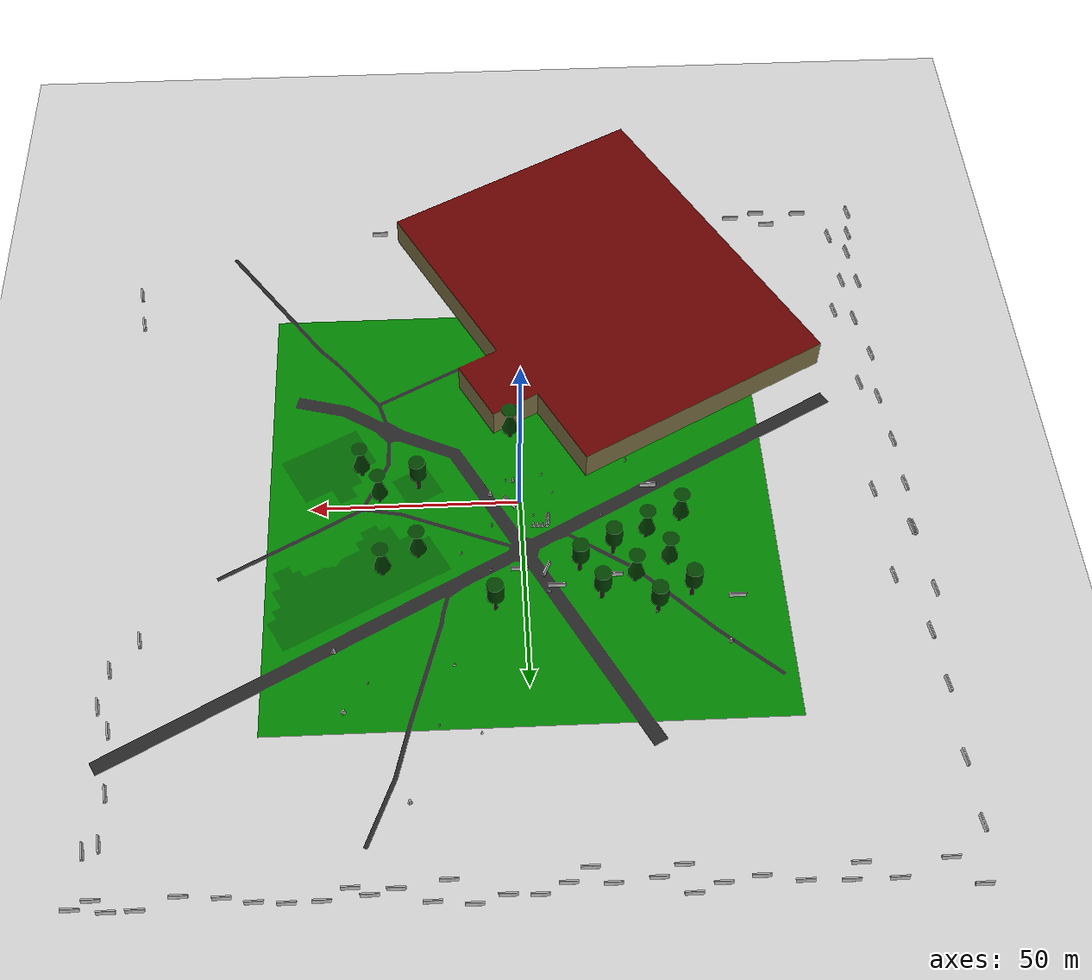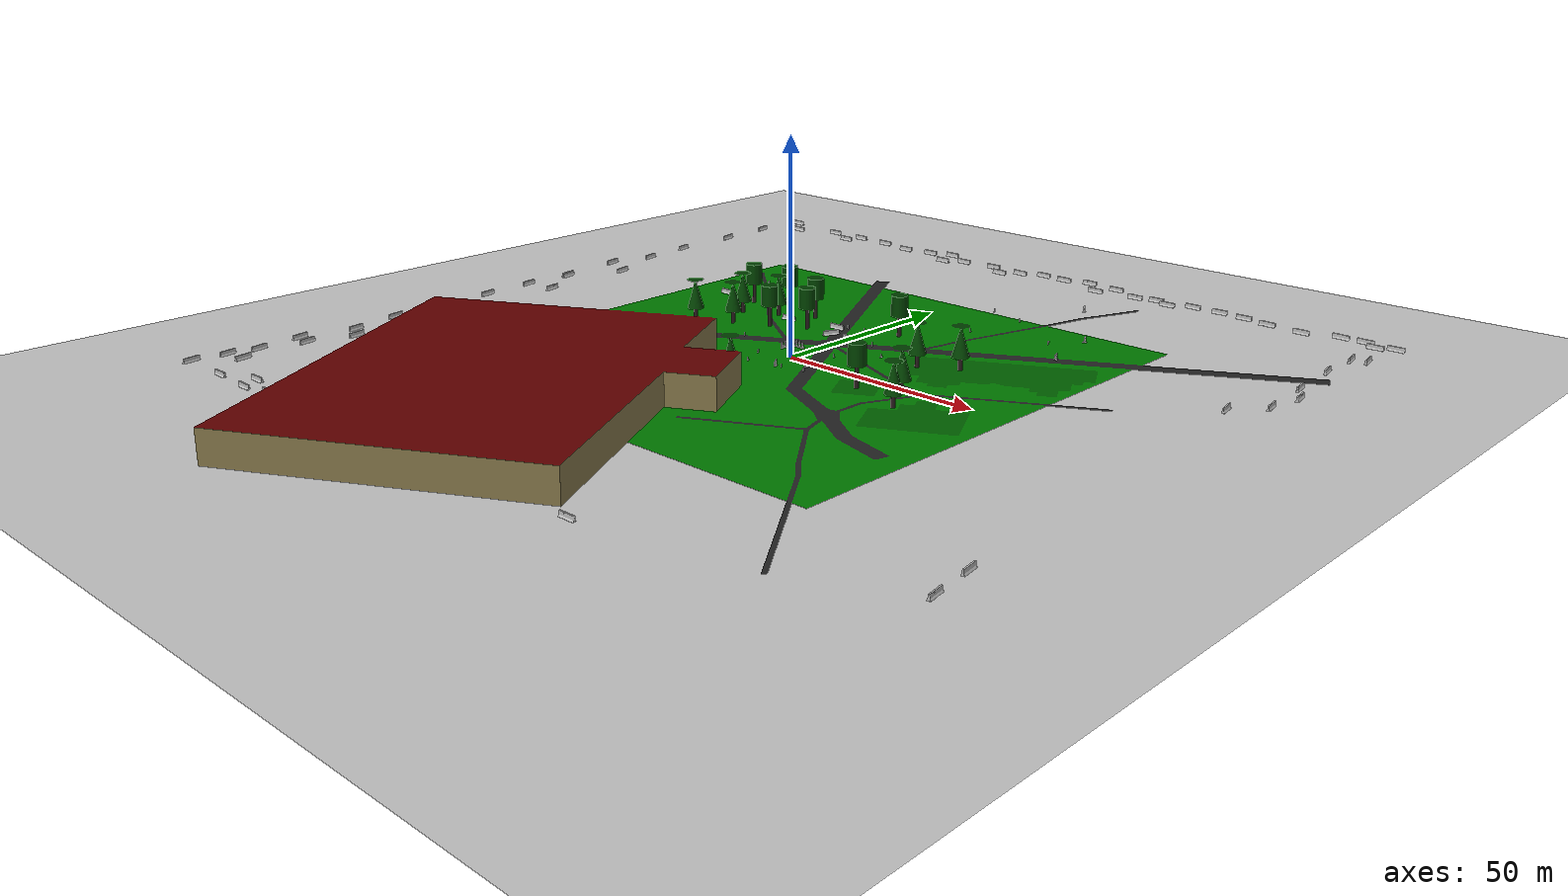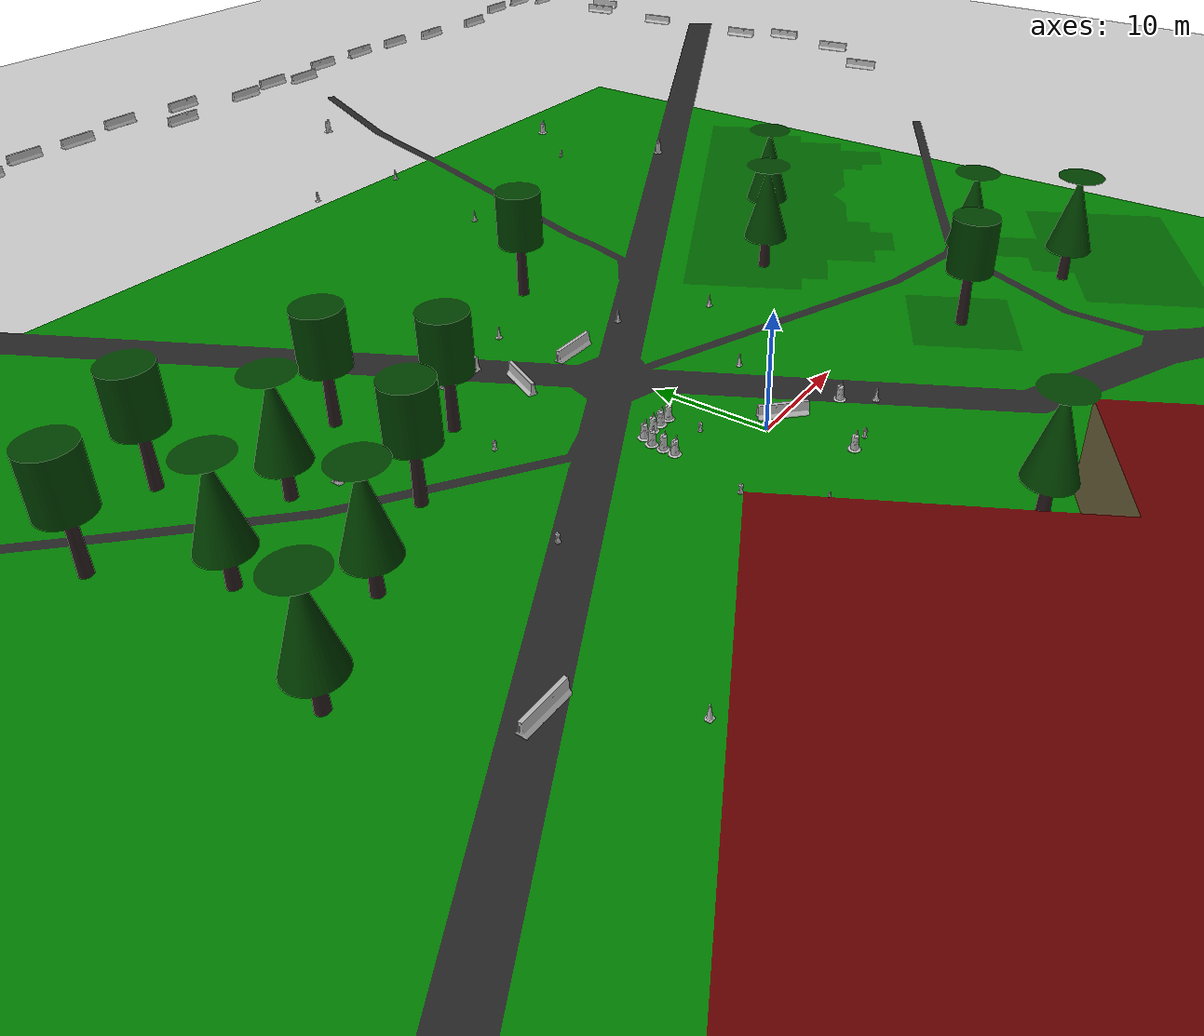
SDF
<sdf version="1.0">
 <world name="default">
  <light name="sun" type="directional">
   <pose>0 0 10 0 -0 0</pose>
   <diffuse>0.8 0.8 0.8 1</diffuse>
   <specular>0.2 0.2 0.2 1</specular>
   <attenuation>
    <range>1000</range>
    <constant>0.9</constant>
    <linear>0.01</linear>
    <quadratic>0.001</quadratic>
   </attenuation>
   <direction>-0.5 0.1 -0.9</direction>
  </light>
  <model name="ground_plane">
   <static>1</static>
   <link name="link">
    <collision name="collision">
     <geometry><plane><normal>0 0 1</normal><size>200 200</size></plane></geometry>
     <surface><friction><ode><mu>100</mu><mu2>50</mu2></ode></friction></surface>
    </collision>
    <visual name="visual">
     <cast_shadows>0</cast_shadows>
     <geometry><plane><normal>0 0 1</normal><size>200 200</size></plane></geometry>
     <material>
      <script><uri>file://media/materials/scripts/gazebo.material</uri><name>Gazebo/Grey</name></script>
     </material>
    </visual>
    <velocity_decay><linear>0</linear><angular>0</angular></velocity_decay>
   </link>
  </model>
  <physics name="default_physics" default="0" type="ode">
   <max_step_size>0.01</max_step_size>
   <real_time_factor>1</real_time_factor>
   <real_time_update_rate>100</real_time_update_rate>
  </physics>
  <scene><ambient>0.4 0.4 0.4 1</ambient><shadows>1</shadows><background>0.7 0.7 0.7 1</background></scene>
  <model name="ubc_campus_structures">
   <pose>0 0 0.001 0 -0 -1.57079632679</pose>
   <static>1</static>
   <link name="link">
    <visual name="top_visual"><geometry><mesh><uri>file://student_union.dae</uri></mesh></geometry></visual>
    <collision name="ubc">
     <pose>0 0 0.001 0 -0 -1.57079632679</pose>
     <geometry><mesh><uri>file://student_union.dae</uri></mesh></geometry>
    </collision>
   </link>
  </model>
  <model name="fire_hydrant">
   <static>1</static>
   <link name="link">
    <collision name="collision">
     <geometry><mesh><uri>model://fire_hydrant/meshes/fire_hydrant.dae</uri></mesh></geometry>
    </collision>
    <visual name="visual">
     <geometry><mesh><uri>model://fire_hydrant/meshes/fire_hydrant.dae</uri></mesh></geometry>
    </visual>
    <velocity_decay><linear>0</linear><angular>0</angular></velocity_decay>
   </link>
   <pose>3.18024 -6.51118 0 0 -0 0</pose>
  </model>
  <model name="fire_hydrant_0">
   <static>1</static>
   <link name="link">
    <collision name="collision">
     <geometry><mesh><uri>model://fire_hydrant/meshes/fire_hydrant.dae</uri></mesh></geometry>
    </collision>
    <visual name="visual">
     <geometry><mesh><uri>model://fire_hydrant/meshes/fire_hydrant.dae</uri></mesh></geometry>
    </visual>
    <velocity_decay><linear>0</linear><angular>0</angular></velocity_decay>
   </link>
   <pose>-3 4 0 0 -0 0</pose>
  </model>
  <model name="fire_hydrant_1">
   <static>1</static>
   <link name="link">
    <collision name="collision">
     <geometry><mesh><uri>model://fire_hydrant/meshes/fire_hydrant.dae</uri></mesh></geometry>
    </collision>
    <visual name="visual">
     <geometry><mesh><uri>model://fire_hydrant/meshes/fire_hydrant.dae</uri></mesh></geometry>
    </visual>
    <velocity_decay><linear>0</linear><angular>0</angular></velocity_decay>
   </link>
   <pose>-7.90686 -2.41363 0 0 -0 0</pose>
  </model>
  <model name="jersey_barrier_15">
   <static>1</static>
   <link name="link">
    <visual name="visual">
     <geometry><mesh><uri>model://jersey_barrier/meshes/jersey_barrier.dae</uri></mesh></geometry>
    </visual>
    <collision name="upright">
     <pose>0 0 0.5715 0 -0 0</pose>
     <geometry><box><size>4.06542 0.3063 1.143</size></box></geometry>
    </collision>
    <collision name="base">
     <pose>0 0 0.032258 0 -0 0</pose>
     <geometry><box><size>4.06542 0.8107 0.064516</size></box></geometry>
    </collision>
    <collision name="base2">
     <pose>0 0 0.1 0 -0 0</pose>
     <geometry><box><size>4.06542 0.65 0.1</size></box></geometry>
    </collision>
    <collision name="base3">
     <pose>0 0 0.2 0 -0 0</pose>
     <geometry><box><size>4.06542 0.5 0.1</size></box></geometry>
    </collision>
    <collision name="left-angle">
     <pose>0 -0.224 0.2401 0.9 -0 0</pose>
     <geometry><box><size>4.06542 0.5 0.064516</size></box></geometry>
    </collision>
    <collision name="right-angle">
     <pose>0 0.224 0.2401 -0.9 0 0</pose>
     <geometry><box><size>4.06542 0.5 0.064516</size></box></geometry>
    </collision>
    <velocity_decay><linear>0</linear><angular>0</angular></velocity_decay>
   </link>
   <pose>2.45495 0 0 0 -0 2.36</pose>
  </model>
  <model name="Construction Cone">
   <link name="link">
    <collision name="collision">
     <geometry>
      <mesh><scale>10 10 10</scale><uri>model://construction_cone/meshes/construction_cone.dae</uri></mesh>
     </geometry>
    </collision>
    <visual name="visual">
     <geometry>
      <mesh><scale>10 10 10</scale><uri>model://construction_cone/meshes/construction_cone.dae</uri></mesh>
     </geometry>
    </visual>
    <velocity_decay><linear>0</linear><angular>0</angular></velocity_decay>
    <inertial>
     <inertia><ixx>1</ixx><ixy>0</ixy><ixz>0</ixz><iyy>1</iyy><iyz>0</iyz><izz>1</izz></inertia>
     <mass>1</mass>
    </inertial>
   </link>
   <pose>-5.59123 -8 0.001963 0 -0.000145 -2e-06</pose>
   <static>0</static>
  </model>
  <model name="Construction Barrel">
   <link name="link">
    <inertial>
     <pose>0 0 0.4 0 -0 0</pose>
     <mass>500</mass>
     <inertia><ixx>51.2096</ixx><iyy>51.2096</iyy><izz>25</izz><ixy>0</ixy><ixz>0</ixz><iyz>0</iyz></inertia>
    </inertial>
    <collision name="collision">
     <geometry><mesh><uri>model://construction_barrel/meshes/construction_barrel.dae</uri></mesh></geometry>
    </collision>
    <visual name="visual">
     <geometry><mesh><uri>model://construction_barrel/meshes/construction_barrel.dae</uri></mesh></geometry>
    </visual>
    <velocity_decay><linear>0</linear><angular>0</angular></velocity_decay>
   </link>
   <pose>7.00245 -2.55681 0.002002 -3.9e-05 2e-05 -0.025507</pose>
   <static>0</static>
  </model>
  <model name="Construction Cone_0">
   <link name="link">
    <collision name="collision">
     <geometry>
      <mesh><scale>10 10 10</scale><uri>model://construction_cone/meshes/construction_cone.dae</uri></mesh>
     </geometry>
    </collision>
    <visual name="visual">
     <geometry>
      <mesh><scale>10 10 10</scale><uri>model://construction_cone/meshes/construction_cone.dae</uri></mesh>
     </geometry>
    </visual>
    <velocity_decay><linear>0</linear><angular>0</angular></velocity_decay>
    <inertial>
     <inertia><ixx>1</ixx><ixy>0</ixy><ixz>0</ixz><iyy>1</iyy><iyz>0</iyz><izz>1</izz></inertia>
     <mass>1</mass>
    </inertial>
   </link>
   <pose>6.99683 6.55732 0.00112 0 -0 -0.007014</pose>
   <static>0</static>
  </model>
  <model name="Construction Barrel_0">
   <link name="link">
    <inertial>
     <pose>0 0 0.4 0 -0 0</pose>
     <mass>500</mass>
     <inertia><ixx>51.2096</ixx><iyy>51.2096</iyy><izz>25</izz><ixy>0</ixy><ixz>0</ixz><iyz>0</iyz></inertia>
    </inertial>
    <collision name="collision">
     <geometry><mesh><uri>model://construction_barrel/meshes/construction_barrel.dae</uri></mesh></geometry>
    </collision>
    <visual name="visual">
     <geometry><mesh><uri>model://construction_barrel/meshes/construction_barrel.dae</uri></mesh></geometry>
    </visual>
    <velocity_decay><linear>0</linear><angular>0</angular></velocity_decay>
   </link>
   <pose>1.44493 -6.51327 0.00196 0.000199 2.5e-05 0.002253</pose>
   <static>0</static>
  </model>
  <model name="Construction Barrel_1">
   <link name="link">
    <inertial>
     <pose>0 0 0.4 0 -0 0</pose>
     <mass>500</mass>
     <inertia><ixx>51.2096</ixx><iyy>51.2096</iyy><izz>25</izz><ixy>0</ixy><ixz>0</ixz><iyz>0</iyz></inertia>
    </inertial>
    <collision name="collision">
     <geometry><mesh><uri>model://construction_barrel/meshes/construction_barrel.dae</uri></mesh></geometry>
    </collision>
    <visual name="visual">
     <geometry><mesh><uri>model://construction_barrel/meshes/construction_barrel.dae</uri></mesh></geometry>
    </visual>
    <velocity_decay><linear>0</linear><angular>0</angular></velocity_decay>
   </link>
   <pose>-6.50125 3.98133 0.001987 3.5e-05 -6.8e-05 -0.017101</pose>
   <static>0</static>
  </model>
  <model name="Construction Barrel_2">
   <link name="link">
    <inertial>
     <pose>0 0 0.4 0 -0 0</pose>
     <mass>500</mass>
     <inertia><ixx>51.2096</ixx><iyy>51.2096</iyy><izz>25</izz><ixy>0</ixy><ixz>0</ixz><iyz>0</iyz></inertia>
    </inertial>
    <collision name="collision">
     <geometry><mesh><uri>model://construction_barrel/meshes/construction_barrel.dae</uri></mesh></geometry>
    </collision>
    <visual name="visual">
     <geometry><mesh><uri>model://construction_barrel/meshes/construction_barrel.dae</uri></mesh></geometry>
    </visual>
    <velocity_decay><linear>0</linear><angular>0</angular></velocity_decay>
   </link>
   <pose>-6.45275 5.00048 0.00168 0.000523 0.000632 0.076262</pose>
   <static>0</static>
  </model>
  <model name="Construction Barrel_3">
   <link name="link">
    <inertial>
     <pose>0 0 0.4 0 -0 0</pose>
     <mass>500</mass>
     <inertia><ixx>51.2096</ixx><iyy>51.2096</iyy><izz>25</izz><ixy>0</ixy><ixz>0</ixz><iyz>0</iyz></inertia>
    </inertial>
    <collision name="collision">
     <geometry><mesh><uri>model://construction_barrel/meshes/construction_barrel.dae</uri></mesh></geometry>
    </collision>
    <visual name="visual">
     <geometry><mesh><uri>model://construction_barrel/meshes/construction_barrel.dae</uri></mesh></geometry>
    </visual>
    <velocity_decay><linear>0</linear><angular>0</angular></velocity_decay>
   </link>
   <pose>-6.42631 6.04619 0.001882 0.000116 -0.000464 -0.022047</pose>
   <static>0</static>
  </model>
  <model name="Construction Barrel_4">
   <link name="link">
    <inertial>
     <pose>0 0 0.4 0 -0 0</pose>
     <mass>500</mass>
     <inertia><ixx>51.2096</ixx><iyy>51.2096</iyy><izz>25</izz><ixy>0</ixy><ixz>0</ixz><iyz>0</iyz></inertia>
    </inertial>
    <collision name="collision">
     <geometry><mesh><uri>model://construction_barrel/meshes/construction_barrel.dae</uri></mesh></geometry>
    </collision>
    <visual name="visual">
     <geometry><mesh><uri>model://construction_barrel/meshes/construction_barrel.dae</uri></mesh></geometry>
    </visual>
    <velocity_decay><linear>0</linear><angular>0</angular></velocity_decay>
   </link>
   <pose>-6.0032 7.01038 0.001769 9.7e-05 0.000741 -0.041558</pose>
   <static>0</static>
  </model>
  <model name="Construction Barrel_5">
   <link name="link">
    <inertial>
     <pose>0 0 0.4 0 -0 0</pose>
     <mass>500</mass>
     <inertia><ixx>51.2096</ixx><iyy>51.2096</iyy><izz>25</izz><ixy>0</ixy><ixz>0</ixz><iyz>0</iyz></inertia>
    </inertial>
    <collision name="collision">
     <geometry><mesh><uri>model://construction_barrel/meshes/construction_barrel.dae</uri></mesh></geometry>
    </collision>
    <visual name="visual">
     <geometry><mesh><uri>model://construction_barrel/meshes/construction_barrel.dae</uri></mesh></geometry>
    </visual>
    <velocity_decay><linear>0</linear><angular>0</angular></velocity_decay>
   </link>
   <pose>-4.90294 7.01071 -0.003568 -1.9e-05 -0.000562 0.157744</pose>
   <static>0</static>
  </model>
  <model name="Construction Barrel_6">
   <link name="link">
    <inertial>
     <pose>0 0 0.4 0 -0 0</pose>
     <mass>500</mass>
     <inertia><ixx>51.2096</ixx><iyy>51.2096</iyy><izz>25</izz><ixy>0</ixy><ixz>0</ixz><iyz>0</iyz></inertia>
    </inertial>
    <collision name="collision">
     <geometry><mesh><uri>model://construction_barrel/meshes/construction_barrel.dae</uri></mesh></geometry>
    </collision>
    <visual name="visual">
     <geometry><mesh><uri>model://construction_barrel/meshes/construction_barrel.dae</uri></mesh></geometry>
    </visual>
    <velocity_decay><linear>0</linear><angular>0</angular></velocity_decay>
   </link>
   <pose>-3.89042 6.9994 0.002 0 -0 -0.093604</pose>
   <static>0</static>
  </model>
  <model name="Construction Barrel_7">
   <link name="link">
    <inertial>
     <pose>0 0 0.4 0 -0 0</pose>
     <mass>500</mass>
     <inertia><ixx>51.2096</ixx><iyy>51.2096</iyy><izz>25</izz><ixy>0</ixy><ixz>0</ixz><iyz>0</iyz></inertia>
    </inertial>
    <collision name="collision">
     <geometry><mesh><uri>model://construction_barrel/meshes/construction_barrel.dae</uri></mesh></geometry>
    </collision>
    <visual name="visual">
     <geometry><mesh><uri>model://construction_barrel/meshes/construction_barrel.dae</uri></mesh></geometry>
    </visual>
    <velocity_decay><linear>0</linear><angular>0</angular></velocity_decay>
   </link>
   <pose>-2.87644 6.95464 0.001974 0.0001 0.000276 0.13686</pose>
   <static>0</static>
  </model>
  <model name="Construction Cone_1">
   <link name="link">
    <collision name="collision">
     <geometry>
      <mesh><scale>10 10 10</scale><uri>model://construction_cone/meshes/construction_cone.dae</uri></mesh>
     </geometry>
    </collision>
    <visual name="visual">
     <geometry>
      <mesh><scale>10 10 10</scale><uri>model://construction_cone/meshes/construction_cone.dae</uri></mesh>
     </geometry>
    </visual>
    <velocity_decay><linear>0</linear><angular>0</angular></velocity_decay>
    <inertial>
     <inertia><ixx>1</ixx><ixy>0</ixy><ixz>0</ixz><iyy>1</iyy><iyz>0</iyz><izz>1</izz></inertia>
     <mass>1</mass>
    </inertial>
   </link>
   <pose>8.42886 -5 0.00112 0 -0 -2e-06</pose>
   <static>0</static>
  </model>
  <spherical_coordinates>
   <latitude_deg>49.2665</latitude_deg>
   <longitude_deg>-123.256</longitude_deg>
   <elevation>91</elevation>
   <surface_model>EARTH_WGS84</surface_model>
   <heading_deg>0</heading_deg>
  </spherical_coordinates>
  <gravity>0 0 -9.8</gravity>
  <magnetic_field>6e-06 2.3e-05 -4.2e-05</magnetic_field>
  <atmosphere type="adiabatic"/>
  <model name="jersey_barrier">
   <static>1</static>
   <link name="link">
    <visual name="visual">
     <geometry><mesh><uri>model://jersey_barrier/meshes/jersey_barrier.dae</uri></mesh></geometry>
    </visual>
    <collision name="upright">
     <pose>0 0 0.5715 0 -0 0</pose>
     <geometry><box><size>4.06542 0.3063 1.143</size></box></geometry>
    </collision>
    <collision name="base">
     <pose>0 0 0.032258 0 -0 0</pose>
     <geometry><box><size>4.06542 0.8107 0.064516</size></box></geometry>
    </collision>
    <collision name="base2">
     <pose>0 0 0.1 0 -0 0</pose>
     <geometry><box><size>4.06542 0.65 0.1</size></box></geometry>
    </collision>
    <collision name="base3">
     <pose>0 0 0.2 0 -0 0</pose>
     <geometry><box><size>4.06542 0.5 0.1</size></box></geometry>
    </collision>
    <collision name="left-angle">
     <pose>0 -0.224 0.2401 0.9 -0 0</pose>
     <geometry><box><size>4.06542 0.5 0.064516</size></box></geometry>
    </collision>
    <collision name="right-angle">
     <pose>0 0.224 0.2401 -0.9 0 0</pose>
     <geometry><box><size>4.06542 0.5 0.064516</size></box></geometry>
    </collision>
   </link>
   <pose>-20.9673 21.5817 0 0 -0 0</pose>
  </model>
  <model name="Construction Cone_2">
   <link name="link">
    <collision name="collision">
     <geometry>
      <mesh><scale>10 10 10</scale><uri>model://construction_cone/meshes/construction_cone.dae</uri></mesh>
     </geometry>
    </collision>
    <visual name="visual">
     <geometry>
      <mesh><scale>10 10 10</scale><uri>model://construction_cone/meshes/construction_cone.dae</uri></mesh>
     </geometry>
    </visual>
    <inertial>
     <inertia><ixx>1</ixx><ixy>0</ixy><ixz>0</ixz><iyy>1</iyy><iyz>0</iyz><izz>1</izz></inertia>
     <mass>1</mass>
    </inertial>
   </link>
   <pose>-0.59762 25.7812 0.002001 0 0 -9.3e-05</pose>
  </model>
  <model name="Construction Cone_3">
   <link name="link">
    <collision name="collision">
     <geometry>
      <mesh><scale>10 10 10</scale><uri>model://construction_cone/meshes/construction_cone.dae</uri></mesh>
     </geometry>
    </collision>
    <visual name="visual">
     <geometry>
      <mesh><scale>10 10 10</scale><uri>model://construction_cone/meshes/construction_cone.dae</uri></mesh>
     </geometry>
    </visual>
    <inertial>
     <inertia><ixx>1</ixx><ixy>0</ixy><ixz>0</ixz><iyy>1</iyy><iyz>0</iyz><izz>1</izz></inertia>
     <mass>1</mass>
    </inertial>
   </link>
   <pose>-3.2139 -31.2066 0.002033 0 0.000135 -1e-06</pose>
  </model>
  <model name="Construction Cone_4">
   <link name="link">
    <collision name="collision">
     <geometry>
      <mesh><scale>10 10 10</scale><uri>model://construction_cone/meshes/construction_cone.dae</uri></mesh>
     </geometry>
    </collision>
    <visual name="visual">
     <geometry>
      <mesh><scale>10 10 10</scale><uri>model://construction_cone/meshes/construction_cone.dae</uri></mesh>
     </geometry>
    </visual>
    <inertial>
     <inertia><ixx>1</ixx><ixy>0</ixy><ixz>0</ixz><iyy>1</iyy><iyz>0</iyz><izz>1</izz></inertia>
     <mass>1</mass>
    </inertial>
   </link>
   <pose>7.48664 19.1243 0.001949 -0 0.000208 -2e-06</pose>
  </model>
  <model name="fire_hydrant_2">
   <static>1</static>
   <link name="link">
    <collision name="collision">
     <geometry><mesh><uri>model://fire_hydrant/meshes/fire_hydrant.dae</uri></mesh></geometry>
    </collision>
    <visual name="visual">
     <geometry><mesh><uri>model://fire_hydrant/meshes/fire_hydrant.dae</uri></mesh></geometry>
    </visual>
   </link>
   <pose>-5.90796 25.8542 0 0 -0 0</pose>
  </model>
  <model name="fire_hydrant_3">
   <static>1</static>
   <link name="link">
    <collision name="collision">
     <geometry><mesh><uri>model://fire_hydrant/meshes/fire_hydrant.dae</uri></mesh></geometry>
    </collision>
    <visual name="visual">
     <geometry><mesh><uri>model://fire_hydrant/meshes/fire_hydrant.dae</uri></mesh></geometry>
    </visual>
   </link>
   <pose>-13.5164 15.0759 0 0 -0 0</pose>
  </model>
  <model name="fire_hydrant_4">
   <static>1</static>
   <link name="link">
    <collision name="collision">
     <geometry><mesh><uri>model://fire_hydrant/meshes/fire_hydrant.dae</uri></mesh></geometry>
    </collision>
    <visual name="visual">
     <geometry><mesh><uri>model://fire_hydrant/meshes/fire_hydrant.dae</uri></mesh></geometry>
    </visual>
   </link>
   <pose>-1.94513 -48.6465 0 0 -0 0</pose>
  </model>
  <model name="Construction Cone_5">
   <link name="link">
    <collision name="collision">
     <geometry>
      <mesh><scale>10 10 10</scale><uri>model://construction_cone/meshes/construction_cone.dae</uri></mesh>
     </geometry>
    </collision>
    <visual name="visual">
     <geometry>
      <mesh><scale>10 10 10</scale><uri>model://construction_cone/meshes/construction_cone.dae</uri></mesh>
     </geometry>
    </visual>
    <inertial>
     <inertia><ixx>1</ixx><ixy>0</ixy><ixz>0</ixz><iyy>1</iyy><iyz>0</iyz><izz>1</izz></inertia>
     <mass>1</mass>
    </inertial>
   </link>
   <pose>14.4618 14.1243 0.001121 0 -0 -2e-06</pose>
  </model>
  <model name="jersey_barrier_0">
   <static>1</static>
   <link name="link">
    <visual name="visual">
     <geometry><mesh><uri>model://jersey_barrier/meshes/jersey_barrier.dae</uri></mesh></geometry>
    </visual>
    <collision name="upright">
     <pose>0 0 0.5715 0 -0 0</pose>
     <geometry><box><size>4.06542 0.3063 1.143</size></box></geometry>
    </collision>
    <collision name="base">
     <pose>0 0 0.032258 0 -0 0</pose>
     <geometry><box><size>4.06542 0.8107 0.064516</size></box></geometry>
    </collision>
    <collision name="base2">
     <pose>0 0 0.1 0 -0 0</pose>
     <geometry><box><size>4.06542 0.65 0.1</size></box></geometry>
    </collision>
    <collision name="base3">
     <pose>0 0 0.2 0 -0 0</pose>
     <geometry><box><size>4.06542 0.5 0.1</size></box></geometry>
    </collision>
    <collision name="left-angle">
     <pose>0 -0.224 0.2401 0.9 -0 0</pose>
     <geometry><box><size>4.06542 0.5 0.064516</size></box></geometry>
    </collision>
    <collision name="right-angle">
     <pose>0 0.224 0.2401 -0.9 0 0</pose>
     <geometry><box><size>4.06542 0.5 0.064516</size></box></geometry>
    </collision>
   </link>
   <pose>-5.2746 19.3549 0 0 -0 1.15044</pose>
  </model>
  <model name="fire_hydrant_5">
   <static>1</static>
   <link name="link">
    <collision name="collision">
     <geometry><mesh><uri>model://fire_hydrant/meshes/fire_hydrant.dae</uri></mesh></geometry>
    </collision>
    <visual name="visual">
     <geometry><mesh><uri>model://fire_hydrant/meshes/fire_hydrant.dae</uri></mesh></geometry>
    </visual>
   </link>
   <pose>-29.9233 32.2758 0 0 -0 0</pose>
  </model>
  <model name="fire_hydrant_6">
   <static>1</static>
   <link name="link">
    <collision name="collision">
     <geometry><mesh><uri>model://fire_hydrant/meshes/fire_hydrant.dae</uri></mesh></geometry>
    </collision>
    <visual name="visual">
     <geometry><mesh><uri>model://fire_hydrant/meshes/fire_hydrant.dae</uri></mesh></geometry>
    </visual>
   </link>
   <pose>-17.6389 -48.9657 0 0 -0 0</pose>
  </model>
  <model name="jersey_barrier_1">
   <static>1</static>
   <link name="link">
    <visual name="visual">
     <geometry><mesh><uri>model://jersey_barrier/meshes/jersey_barrier.dae</uri></mesh></geometry>
    </visual>
    <collision name="upright">
     <pose>0 0 0.5715 0 -0 0</pose>
     <geometry><box><size>4.06542 0.3063 1.143</size></box></geometry>
    </collision>
    <collision name="base">
     <pose>0 0 0.032258 0 -0 0</pose>
     <geometry><box><size>4.06542 0.8107 0.064516</size></box></geometry>
    </collision>
    <collision name="base2">
     <pose>0 0 0.1 0 -0 0</pose>
     <geometry><box><size>4.06542 0.65 0.1</size></box></geometry>
    </collision>
    <collision name="base3">
     <pose>0 0 0.2 0 -0 0</pose>
     <geometry><box><size>4.06542 0.5 0.1</size></box></geometry>
    </collision>
    <collision name="left-angle">
     <pose>0 -0.224 0.2401 0.9 -0 0</pose>
     <geometry><box><size>4.06542 0.5 0.064516</size></box></geometry>
    </collision>
    <collision name="right-angle">
     <pose>0 0.224 0.2401 -0.9 0 0</pose>
     <geometry><box><size>4.06542 0.5 0.064516</size></box></geometry>
    </collision>
   </link>
   <pose>-31.1133 -3.70786 0 0 -0 0</pose>
  </model>
  <model name="fire_hydrant_7">
   <static>1</static>
   <link name="link">
    <collision name="collision">
     <geometry><mesh><uri>model://fire_hydrant/meshes/fire_hydrant.dae</uri></mesh></geometry>
    </collision>
    <visual name="visual">
     <geometry><mesh><uri>model://fire_hydrant/meshes/fire_hydrant.dae</uri></mesh></geometry>
    </visual>
   </link>
   <pose>-2.26232 -34.1417 0 0 -0 0</pose>
  </model>
  <model name="jersey_barrier_2">
   <static>1</static>
   <link name="link">
    <visual name="visual">
     <geometry><mesh><uri>model://jersey_barrier/meshes/jersey_barrier.dae</uri></mesh></geometry>
    </visual>
    <collision name="upright">
     <pose>0 0 0.5715 0 -0 0</pose>
     <geometry><box><size>4.06542 0.3063 1.143</size></box></geometry>
    </collision>
    <collision name="base">
     <pose>0 0 0.032258 0 -0 0</pose>
     <geometry><box><size>4.06542 0.8107 0.064516</size></box></geometry>
    </collision>
    <collision name="base2">
     <pose>0 0 0.1 0 -0 0</pose>
     <geometry><box><size>4.06542 0.65 0.1</size></box></geometry>
    </collision>
    <collision name="base3">
     <pose>0 0 0.2 0 -0 0</pose>
     <geometry><box><size>4.06542 0.5 0.1</size></box></geometry>
    </collision>
    <collision name="left-angle">
     <pose>0 -0.224 0.2401 0.9 -0 0</pose>
     <geometry><box><size>4.06542 0.5 0.064516</size></box></geometry>
    </collision>
    <collision name="right-angle">
     <pose>0 0.224 0.2401 -0.9 0 0</pose>
     <geometry><box><size>4.06542 0.5 0.064516</size></box></geometry>
    </collision>
   </link>
   <pose>0.987338 19.0398 0 0 -0 0</pose>
  </model>
  <model name="jersey_barrier_3">
   <static>1</static>
   <link name="link">
    <visual name="visual">
     <geometry><mesh><uri>model://jersey_barrier/meshes/jersey_barrier.dae</uri></mesh></geometry>
    </visual>
    <collision name="upright">
     <pose>0 0 0.5715 0 -0 0</pose>
     <geometry><box><size>4.06542 0.3063 1.143</size></box></geometry>
    </collision>
    <collision name="base">
     <pose>0 0 0.032258 0 -0 0</pose>
     <geometry><box><size>4.06542 0.8107 0.064516</size></box></geometry>
    </collision>
    <collision name="base2">
     <pose>0 0 0.1 0 -0 0</pose>
     <geometry><box><size>4.06542 0.65 0.1</size></box></geometry>
    </collision>
    <collision name="base3">
     <pose>0 0 0.2 0 -0 0</pose>
     <geometry><box><size>4.06542 0.5 0.1</size></box></geometry>
    </collision>
    <collision name="left-angle">
     <pose>0 -0.224 0.2401 0.9 -0 0</pose>
     <geometry><box><size>4.06542 0.5 0.064516</size></box></geometry>
    </collision>
    <collision name="right-angle">
     <pose>0 0.224 0.2401 -0.9 0 0</pose>
     <geometry><box><size>4.06542 0.5 0.064516</size></box></geometry>
    </collision>
   </link>
   <pose>96.2925 97.4858 0 0 -0 0</pose>
  </model>
  <model name="jersey_barrier_4">
   <static>1</static>
   <link name="link">
    <visual name="visual">
     <geometry><mesh><uri>model://jersey_barrier/meshes/jersey_barrier.dae</uri></mesh></geometry>
    </visual>
    <collision name="upright">
     <pose>0 0 0.5715 0 -0 0</pose>
     <geometry><box><size>4.06542 0.3063 1.143</size></box></geometry>
    </collision>
    <collision name="base">
     <pose>0 0 0.032258 0 -0 0</pose>
     <geometry><box><size>4.06542 0.8107 0.064516</size></box></geometry>
    </collision>
    <collision name="base2">
     <pose>0 0 0.1 0 -0 0</pose>
     <geometry><box><size>4.06542 0.65 0.1</size></box></geometry>
    </collision>
    <collision name="base3">
     <pose>0 0 0.2 0 -0 0</pose>
     <geometry><box><size>4.06542 0.5 0.1</size></box></geometry>
    </collision>
    <collision name="left-angle">
     <pose>0 -0.224 0.2401 0.9 -0 0</pose>
     <geometry><box><size>4.06542 0.5 0.064516</size></box></geometry>
    </collision>
    <collision name="right-angle">
     <pose>0 0.224 0.2401 -0.9 0 0</pose>
     <geometry><box><size>4.06542 0.5 0.064516</size></box></geometry>
    </collision>
   </link>
   <pose>88.8818 98.2918 0 0 -0 0</pose>
  </model>
  <model name="jersey_barrier_5">
   <static>1</static>
   <link name="link">
    <visual name="visual">
     <geometry><mesh><uri>model://jersey_barrier/meshes/jersey_barrier.dae</uri></mesh></geometry>
    </visual>
    <collision name="upright">
     <pose>0 0 0.5715 0 -0 0</pose>
     <geometry><box><size>4.06542 0.3063 1.143</size></box></geometry>
    </collision>
    <collision name="base">
     <pose>0 0 0.032258 0 -0 0</pose>
     <geometry><box><size>4.06542 0.8107 0.064516</size></box></geometry>
    </collision>
    <collision name="base2">
     <pose>0 0 0.1 0 -0 0</pose>
     <geometry><box><size>4.06542 0.65 0.1</size></box></geometry>
    </collision>
    <collision name="base3">
     <pose>0 0 0.2 0 -0 0</pose>
     <geometry><box><size>4.06542 0.5 0.1</size></box></geometry>
    </collision>
    <collision name="left-angle">
     <pose>0 -0.224 0.2401 0.9 -0 0</pose>
     <geometry><box><size>4.06542 0.5 0.064516</size></box></geometry>
    </collision>
    <collision name="right-angle">
     <pose>0 0.224 0.2401 -0.9 0 0</pose>
     <geometry><box><size>4.06542 0.5 0.064516</size></box></geometry>
    </collision>
   </link>
   <pose>92.2417 95.6614 0 0 -0 0</pose>
  </model>
  <model name="jersey_barrier_6">
   <static>1</static>
   <link name="link">
    <visual name="visual">
     <geometry><mesh><uri>model://jersey_barrier/meshes/jersey_barrier.dae</uri></mesh></geometry>
    </visual>
    <collision name="upright">
     <pose>0 0 0.5715 0 -0 0</pose>
     <geometry><box><size>4.06542 0.3063 1.143</size></box></geometry>
    </collision>
    <collision name="base">
     <pose>0 0 0.032258 0 -0 0</pose>
     <geometry><box><size>4.06542 0.8107 0.064516</size></box></geometry>
    </collision>
    <collision name="base2">
     <pose>0 0 0.1 0 -0 0</pose>
     <geometry><box><size>4.06542 0.65 0.1</size></box></geometry>
    </collision>
    <collision name="base3">
     <pose>0 0 0.2 0 -0 0</pose>
     <geometry><box><size>4.06542 0.5 0.1</size></box></geometry>
    </collision>
    <collision name="left-angle">
     <pose>0 -0.224 0.2401 0.9 -0 0</pose>
     <geometry><box><size>4.06542 0.5 0.064516</size></box></geometry>
    </collision>
    <collision name="right-angle">
     <pose>0 0.224 0.2401 -0.9 0 0</pose>
     <geometry><box><size>4.06542 0.5 0.064516</size></box></geometry>
    </collision>
   </link>
   <pose>83.0097 98.1997 0 0 -0 0</pose>
  </model>
  <model name="jersey_barrier_7">
   <static>1</static>
   <link name="link">
    <visual name="visual">
     <geometry><mesh><uri>model://jersey_barrier/meshes/jersey_barrier.dae</uri></mesh></geometry>
    </visual>
    <collision name="upright">
     <pose>0 0 0.5715 0 -0 0</pose>
     <geometry><box><size>4.06542 0.3063 1.143</size></box></geometry>
    </collision>
    <collision name="base">
     <pose>0 0 0.032258 0 -0 0</pose>
     <geometry><box><size>4.06542 0.8107 0.064516</size></box></geometry>
    </collision>
    <collision name="base2">
     <pose>0 0 0.1 0 -0 0</pose>
     <geometry><box><size>4.06542 0.65 0.1</size></box></geometry>
    </collision>
    <collision name="base3">
     <pose>0 0 0.2 0 -0 0</pose>
     <geometry><box><size>4.06542 0.5 0.1</size></box></geometry>
    </collision>
    <collision name="left-angle">
     <pose>0 -0.224 0.2401 0.9 -0 0</pose>
     <geometry><box><size>4.06542 0.5 0.064516</size></box></geometry>
    </collision>
    <collision name="right-angle">
     <pose>0 0.224 0.2401 -0.9 0 0</pose>
     <geometry><box><size>4.06542 0.5 0.064516</size></box></geometry>
    </collision>
   </link>
   <pose>74.4894 95.5567 0 0 -0 0</pose>
  </model>
  <model name="jersey_barrier_8">
   <static>1</static>
   <link name="link">
    <visual name="visual">
     <geometry><mesh><uri>model://jersey_barrier/meshes/jersey_barrier.dae</uri></mesh></geometry>
    </visual>
    <collision name="upright">
     <pose>0 0 0.5715 0 -0 0</pose>
     <geometry><box><size>4.06542 0.3063 1.143</size></box></geometry>
    </collision>
    <collision name="base">
     <pose>0 0 0.032258 0 -0 0</pose>
     <geometry><box><size>4.06542 0.8107 0.064516</size></box></geometry>
    </collision>
    <collision name="base2">
     <pose>0 0 0.1 0 -0 0</pose>
     <geometry><box><size>4.06542 0.65 0.1</size></box></geometry>
    </collision>
    <collision name="base3">
     <pose>0 0 0.2 0 -0 0</pose>
     <geometry><box><size>4.06542 0.5 0.1</size></box></geometry>
    </collision>
    <collision name="left-angle">
     <pose>0 -0.224 0.2401 0.9 -0 0</pose>
     <geometry><box><size>4.06542 0.5 0.064516</size></box></geometry>
    </collision>
    <collision name="right-angle">
     <pose>0 0.224 0.2401 -0.9 0 0</pose>
     <geometry><box><size>4.06542 0.5 0.064516</size></box></geometry>
    </collision>
   </link>
   <pose>65.5701 96.2619 0 0 -0 0</pose>
  </model>
  <model name="jersey_barrier_9">
   <static>1</static>
   <link name="link">
    <visual name="visual">
     <geometry><mesh><uri>model://jersey_barrier/meshes/jersey_barrier.dae</uri></mesh></geometry>
    </visual>
    <collision name="upright">
     <pose>0 0 0.5715 0 -0 0</pose>
     <geometry><box><size>4.06542 0.3063 1.143</size></box></geometry>
    </collision>
    <collision name="base">
     <pose>0 0 0.032258 0 -0 0</pose>
     <geometry><box><size>4.06542 0.8107 0.064516</size></box></geometry>
    </collision>
    <collision name="base2">
     <pose>0 0 0.1 0 -0 0</pose>
     <geometry><box><size>4.06542 0.65 0.1</size></box></geometry>
    </collision>
    <collision name="base3">
     <pose>0 0 0.2 0 -0 0</pose>
     <geometry><box><size>4.06542 0.5 0.1</size></box></geometry>
    </collision>
    <collision name="left-angle">
     <pose>0 -0.224 0.2401 0.9 -0 0</pose>
     <geometry><box><size>4.06542 0.5 0.064516</size></box></geometry>
    </collision>
    <collision name="right-angle">
     <pose>0 0.224 0.2401 -0.9 0 0</pose>
     <geometry><box><size>4.06542 0.5 0.064516</size></box></geometry>
    </collision>
   </link>
   <pose>58.9738 97.4742 0 0 -0 0</pose>
  </model>
  <model name="jersey_barrier_10">
   <static>1</static>
   <link name="link">
    <visual name="visual">
     <geometry><mesh><uri>model://jersey_barrier/meshes/jersey_barrier.dae</uri></mesh></geometry>
    </visual>
    <collision name="upright">
     <pose>0 0 0.5715 0 -0 0</pose>
     <geometry><box><size>4.06542 0.3063 1.143</size></box></geometry>
    </collision>
    <collision name="base">
     <pose>0 0 0.032258 0 -0 0</pose>
     <geometry><box><size>4.06542 0.8107 0.064516</size></box></geometry>
    </collision>
    <collision name="base2">
     <pose>0 0 0.1 0 -0 0</pose>
     <geometry><box><size>4.06542 0.65 0.1</size></box></geometry>
    </collision>
    <collision name="base3">
     <pose>0 0 0.2 0 -0 0</pose>
     <geometry><box><size>4.06542 0.5 0.1</size></box></geometry>
    </collision>
    <collision name="left-angle">
     <pose>0 -0.224 0.2401 0.9 -0 0</pose>
     <geometry><box><size>4.06542 0.5 0.064516</size></box></geometry>
    </collision>
    <collision name="right-angle">
     <pose>0 0.224 0.2401 -0.9 0 0</pose>
     <geometry><box><size>4.06542 0.5 0.064516</size></box></geometry>
    </collision>
   </link>
   <pose>52.2741 97.9566 0 0 -0 0</pose>
  </model>
  <model name="jersey_barrier_11">
   <static>1</static>
   <link name="link">
    <visual name="visual">
     <geometry><mesh><uri>model://jersey_barrier/meshes/jersey_barrier.dae</uri></mesh></geometry>
    </visual>
    <collision name="upright">
     <pose>0 0 0.5715 0 -0 0</pose>
     <geometry><box><size>4.06542 0.3063 1.143</size></box></geometry>
    </collision>
    <collision name="base">
     <pose>0 0 0.032258 0 -0 0</pose>
     <geometry><box><size>4.06542 0.8107 0.064516</size></box></geometry>
    </collision>
    <collision name="base2">
     <pose>0 0 0.1 0 -0 0</pose>
     <geometry><box><size>4.06542 0.65 0.1</size></box></geometry>
    </collision>
    <collision name="base3">
     <pose>0 0 0.2 0 -0 0</pose>
     <geometry><box><size>4.06542 0.5 0.1</size></box></geometry>
    </collision>
    <collision name="left-angle">
     <pose>0 -0.224 0.2401 0.9 -0 0</pose>
     <geometry><box><size>4.06542 0.5 0.064516</size></box></geometry>
    </collision>
    <collision name="right-angle">
     <pose>0 0.224 0.2401 -0.9 0 0</pose>
     <geometry><box><size>4.06542 0.5 0.064516</size></box></geometry>
    </collision>
   </link>
   <pose>45.0807 97.7999 0 0 -0 0</pose>
  </model>
  <model name="jersey_barrier_12">
   <static>1</static>
   <link name="link">
    <visual name="visual">
     <geometry><mesh><uri>model://jersey_barrier/meshes/jersey_barrier.dae</uri></mesh></geometry>
    </visual>
    <collision name="upright">
     <pose>0 0 0.5715 0 -0 0</pose>
     <geometry><box><size>4.06542 0.3063 1.143</size></box></geometry>
    </collision>
    <collision name="base">
     <pose>0 0 0.032258 0 -0 0</pose>
     <geometry><box><size>4.06542 0.8107 0.064516</size></box></geometry>
    </collision>
    <collision name="base2">
     <pose>0 0 0.1 0 -0 0</pose>
     <geometry><box><size>4.06542 0.65 0.1</size></box></geometry>
    </collision>
    <collision name="base3">
     <pose>0 0 0.2 0 -0 0</pose>
     <geometry><box><size>4.06542 0.5 0.1</size></box></geometry>
    </collision>
    <collision name="left-angle">
     <pose>0 -0.224 0.2401 0.9 -0 0</pose>
     <geometry><box><size>4.06542 0.5 0.064516</size></box></geometry>
    </collision>
    <collision name="right-angle">
     <pose>0 0.224 0.2401 -0.9 0 0</pose>
     <geometry><box><size>4.06542 0.5 0.064516</size></box></geometry>
    </collision>
   </link>
   <pose>35.3415 96.9572 0 0 -0 0</pose>
  </model>
  <model name="jersey_barrier_13">
   <static>1</static>
   <link name="link">
    <visual name="visual">
     <geometry><mesh><uri>model://jersey_barrier/meshes/jersey_barrier.dae</uri></mesh></geometry>
    </visual>
    <collision name="upright">
     <pose>0 0 0.5715 0 -0 0</pose>
     <geometry><box><size>4.06542 0.3063 1.143</size></box></geometry>
    </collision>
    <collision name="base">
     <pose>0 0 0.032258 0 -0 0</pose>
     <geometry><box><size>4.06542 0.8107 0.064516</size></box></geometry>
    </collision>
    <collision name="base2">
     <pose>0 0 0.1 0 -0 0</pose>
     <geometry><box><size>4.06542 0.65 0.1</size></box></geometry>
    </collision>
    <collision name="base3">
     <pose>0 0 0.2 0 -0 0</pose>
     <geometry><box><size>4.06542 0.5 0.1</size></box></geometry>
    </collision>
    <collision name="left-angle">
     <pose>0 -0.224 0.2401 0.9 -0 0</pose>
     <geometry><box><size>4.06542 0.5 0.064516</size></box></geometry>
    </collision>
    <collision name="right-angle">
     <pose>0 0.224 0.2401 -0.9 0 0</pose>
     <geometry><box><size>4.06542 0.5 0.064516</size></box></geometry>
    </collision>
   </link>
   <pose>39.3518 95.2275 0 0 -0 0</pose>
  </model>
  <model name="jersey_barrier_14">
   <static>1</static>
   <link name="link">
    <visual name="visual">
     <geometry><mesh><uri>model://jersey_barrier/meshes/jersey_barrier.dae</uri></mesh></geometry>
    </visual>
    <collision name="upright">
     <pose>0 0 0.5715 0 -0 0</pose>
     <geometry><box><size>4.06542 0.3063 1.143</size></box></geometry>
    </collision>
    <collision name="base">
     <pose>0 0 0.032258 0 -0 0</pose>
     <geometry><box><size>4.06542 0.8107 0.064516</size></box></geometry>
    </collision>
    <collision name="base2">
     <pose>0 0 0.1 0 -0 0</pose>
     <geometry><box><size>4.06542 0.65 0.1</size></box></geometry>
    </collision>
    <collision name="base3">
     <pose>0 0 0.2 0 -0 0</pose>
     <geometry><box><size>4.06542 0.5 0.1</size></box></geometry>
    </collision>
    <collision name="left-angle">
     <pose>0 -0.224 0.2401 0.9 -0 0</pose>
     <geometry><box><size>4.06542 0.5 0.064516</size></box></geometry>
    </collision>
    <collision name="right-angle">
     <pose>0 0.224 0.2401 -0.9 0 0</pose>
     <geometry><box><size>4.06542 0.5 0.064516</size></box></geometry>
    </collision>
   </link>
   <pose>29.9046 95.7893 0 0 -0 0</pose>
  </model>
  <model name="jersey_barrier_16">
   <static>1</static>
   <link name="link">
    <visual name="visual">
     <geometry><mesh><uri>model://jersey_barrier/meshes/jersey_barrier.dae</uri></mesh></geometry>
    </visual>
    <collision name="upright">
     <pose>0 0 0.5715 0 -0 0</pose>
     <geometry><box><size>4.06542 0.3063 1.143</size></box></geometry>
    </collision>
    <collision name="base">
     <pose>0 0 0.032258 0 -0 0</pose>
     <geometry><box><size>4.06542 0.8107 0.064516</size></box></geometry>
    </collision>
    <collision name="base2">
     <pose>0 0 0.1 0 -0 0</pose>
     <geometry><box><size>4.06542 0.65 0.1</size></box></geometry>
    </collision>
    <collision name="base3">
     <pose>0 0 0.2 0 -0 0</pose>
     <geometry><box><size>4.06542 0.5 0.1</size></box></geometry>
    </collision>
    <collision name="left-angle">
     <pose>0 -0.224 0.2401 0.9 -0 0</pose>
     <geometry><box><size>4.06542 0.5 0.064516</size></box></geometry>
    </collision>
    <collision name="right-angle">
     <pose>0 0.224 0.2401 -0.9 0 0</pose>
     <geometry><box><size>4.06542 0.5 0.064516</size></box></geometry>
    </collision>
   </link>
   <pose>22.4772 98.9588 0 0 -0 0</pose>
  </model>
  <model name="jersey_barrier_17">
   <static>1</static>
   <link name="link">
    <visual name="visual">
     <geometry><mesh><uri>model://jersey_barrier/meshes/jersey_barrier.dae</uri></mesh></geometry>
    </visual>
    <collision name="upright">
     <pose>0 0 0.5715 0 -0 0</pose>
     <geometry><box><size>4.06542 0.3063 1.143</size></box></geometry>
    </collision>
    <collision name="base">
     <pose>0 0 0.032258 0 -0 0</pose>
     <geometry><box><size>4.06542 0.8107 0.064516</size></box></geometry>
    </collision>
    <collision name="base2">
     <pose>0 0 0.1 0 -0 0</pose>
     <geometry><box><size>4.06542 0.65 0.1</size></box></geometry>
    </collision>
    <collision name="base3">
     <pose>0 0 0.2 0 -0 0</pose>
     <geometry><box><size>4.06542 0.5 0.1</size></box></geometry>
    </collision>
    <collision name="left-angle">
     <pose>0 -0.224 0.2401 0.9 -0 0</pose>
     <geometry><box><size>4.06542 0.5 0.064516</size></box></geometry>
    </collision>
    <collision name="right-angle">
     <pose>0 0.224 0.2401 -0.9 0 0</pose>
     <geometry><box><size>4.06542 0.5 0.064516</size></box></geometry>
    </collision>
   </link>
   <pose>13.8876 99.8015 0 0 -0 0</pose>
  </model>
  <model name="jersey_barrier_18">
   <static>1</static>
   <link name="link">
    <visual name="visual">
     <geometry><mesh><uri>model://jersey_barrier/meshes/jersey_barrier.dae</uri></mesh></geometry>
    </visual>
    <collision name="upright">
     <pose>0 0 0.5715 0 -0 0</pose>
     <geometry><box><size>4.06542 0.3063 1.143</size></box></geometry>
    </collision>
    <collision name="base">
     <pose>0 0 0.032258 0 -0 0</pose>
     <geometry><box><size>4.06542 0.8107 0.064516</size></box></geometry>
    </collision>
    <collision name="base2">
     <pose>0 0 0.1 0 -0 0</pose>
     <geometry><box><size>4.06542 0.65 0.1</size></box></geometry>
    </collision>
    <collision name="base3">
     <pose>0 0 0.2 0 -0 0</pose>
     <geometry><box><size>4.06542 0.5 0.1</size></box></geometry>
    </collision>
    <collision name="left-angle">
     <pose>0 -0.224 0.2401 0.9 -0 0</pose>
     <geometry><box><size>4.06542 0.5 0.064516</size></box></geometry>
    </collision>
    <collision name="right-angle">
     <pose>0 0.224 0.2401 -0.9 0 0</pose>
     <geometry><box><size>4.06542 0.5 0.064516</size></box></geometry>
    </collision>
   </link>
   <pose>19.0417 94.3609 0 0 -0 0</pose>
  </model>
  <model name="jersey_barrier_19">
   <static>1</static>
   <link name="link">
    <visual name="visual">
     <geometry><mesh><uri>model://jersey_barrier/meshes/jersey_barrier.dae</uri></mesh></geometry>
    </visual>
    <collision name="upright">
     <pose>0 0 0.5715 0 -0 0</pose>
     <geometry><box><size>4.06542 0.3063 1.143</size></box></geometry>
    </collision>
    <collision name="base">
     <pose>0 0 0.032258 0 -0 0</pose>
     <geometry><box><size>4.06542 0.8107 0.064516</size></box></geometry>
    </collision>
    <collision name="base2">
     <pose>0 0 0.1 0 -0 0</pose>
     <geometry><box><size>4.06542 0.65 0.1</size></box></geometry>
    </collision>
    <collision name="base3">
     <pose>0 0 0.2 0 -0 0</pose>
     <geometry><box><size>4.06542 0.5 0.1</size></box></geometry>
    </collision>
    <collision name="left-angle">
     <pose>0 -0.224 0.2401 0.9 -0 0</pose>
     <geometry><box><size>4.06542 0.5 0.064516</size></box></geometry>
    </collision>
    <collision name="right-angle">
     <pose>0 0.224 0.2401 -0.9 0 0</pose>
     <geometry><box><size>4.06542 0.5 0.064516</size></box></geometry>
    </collision>
   </link>
   <pose>7.01473 98.1013 0 0 -0 0</pose>
  </model>
  <model name="jersey_barrier_20">
   <static>1</static>
   <link name="link">
    <visual name="visual">
     <geometry><mesh><uri>model://jersey_barrier/meshes/jersey_barrier.dae</uri></mesh></geometry>
    </visual>
    <collision name="upright">
     <pose>0 0 0.5715 0 -0 0</pose>
     <geometry><box><size>4.06542 0.3063 1.143</size></box></geometry>
    </collision>
    <collision name="base">
     <pose>0 0 0.032258 0 -0 0</pose>
     <geometry><box><size>4.06542 0.8107 0.064516</size></box></geometry>
    </collision>
    <collision name="base2">
     <pose>0 0 0.1 0 -0 0</pose>
     <geometry><box><size>4.06542 0.65 0.1</size></box></geometry>
    </collision>
    <collision name="base3">
     <pose>0 0 0.2 0 -0 0</pose>
     <geometry><box><size>4.06542 0.5 0.1</size></box></geometry>
    </collision>
    <collision name="left-angle">
     <pose>0 -0.224 0.2401 0.9 -0 0</pose>
     <geometry><box><size>4.06542 0.5 0.064516</size></box></geometry>
    </collision>
    <collision name="right-angle">
     <pose>0 0.224 0.2401 -0.9 0 0</pose>
     <geometry><box><size>4.06542 0.5 0.064516</size></box></geometry>
    </collision>
   </link>
   <pose>0.430173 98.3822 0 0 -0 0</pose>
  </model>
  <model name="jersey_barrier_21">
   <static>1</static>
   <link name="link">
    <visual name="visual">
     <geometry><mesh><uri>model://jersey_barrier/meshes/jersey_barrier.dae</uri></mesh></geometry>
    </visual>
    <collision name="upright">
     <pose>0 0 0.5715 0 -0 0</pose>
     <geometry><box><size>4.06542 0.3063 1.143</size></box></geometry>
    </collision>
    <collision name="base">
     <pose>0 0 0.032258 0 -0 0</pose>
     <geometry><box><size>4.06542 0.8107 0.064516</size></box></geometry>
    </collision>
    <collision name="base2">
     <pose>0 0 0.1 0 -0 0</pose>
     <geometry><box><size>4.06542 0.65 0.1</size></box></geometry>
    </collision>
    <collision name="base3">
     <pose>0 0 0.2 0 -0 0</pose>
     <geometry><box><size>4.06542 0.5 0.1</size></box></geometry>
    </collision>
    <collision name="left-angle">
     <pose>0 -0.224 0.2401 0.9 -0 0</pose>
     <geometry><box><size>4.06542 0.5 0.064516</size></box></geometry>
    </collision>
    <collision name="right-angle">
     <pose>0 0.224 0.2401 -0.9 0 0</pose>
     <geometry><box><size>4.06542 0.5 0.064516</size></box></geometry>
    </collision>
   </link>
   <pose>-5.58333 96.0759 0 0 -0 0</pose>
  </model>
  <model name="jersey_barrier_22">
   <static>1</static>
   <link name="link">
    <visual name="visual">
     <geometry><mesh><uri>model://jersey_barrier/meshes/jersey_barrier.dae</uri></mesh></geometry>
    </visual>
    <collision name="upright">
     <pose>0 0 0.5715 0 -0 0</pose>
     <geometry><box><size>4.06542 0.3063 1.143</size></box></geometry>
    </collision>
    <collision name="base">
     <pose>0 0 0.032258 0 -0 0</pose>
     <geometry><box><size>4.06542 0.8107 0.064516</size></box></geometry>
    </collision>
    <collision name="base2">
     <pose>0 0 0.1 0 -0 0</pose>
     <geometry><box><size>4.06542 0.65 0.1</size></box></geometry>
    </collision>
    <collision name="base3">
     <pose>0 0 0.2 0 -0 0</pose>
     <geometry><box><size>4.06542 0.5 0.1</size></box></geometry>
    </collision>
    <collision name="left-angle">
     <pose>0 -0.224 0.2401 0.9 -0 0</pose>
     <geometry><box><size>4.06542 0.5 0.064516</size></box></geometry>
    </collision>
    <collision name="right-angle">
     <pose>0 0.224 0.2401 -0.9 0 0</pose>
     <geometry><box><size>4.06542 0.5 0.064516</size></box></geometry>
    </collision>
   </link>
   <pose>-14.7441 96.6524 0 0 -0 0</pose>
  </model>
  <model name="jersey_barrier_23">
   <static>1</static>
   <link name="link">
    <visual name="visual">
     <geometry><mesh><uri>model://jersey_barrier/meshes/jersey_barrier.dae</uri></mesh></geometry>
    </visual>
    <collision name="upright">
     <pose>0 0 0.5715 0 -0 0</pose>
     <geometry><box><size>4.06542 0.3063 1.143</size></box></geometry>
    </collision>
    <collision name="base">
     <pose>0 0 0.032258 0 -0 0</pose>
     <geometry><box><size>4.06542 0.8107 0.064516</size></box></geometry>
    </collision>
    <collision name="base2">
     <pose>0 0 0.1 0 -0 0</pose>
     <geometry><box><size>4.06542 0.65 0.1</size></box></geometry>
    </collision>
    <collision name="base3">
     <pose>0 0 0.2 0 -0 0</pose>
     <geometry><box><size>4.06542 0.5 0.1</size></box></geometry>
    </collision>
    <collision name="left-angle">
     <pose>0 -0.224 0.2401 0.9 -0 0</pose>
     <geometry><box><size>4.06542 0.5 0.064516</size></box></geometry>
    </collision>
    <collision name="right-angle">
     <pose>0 0.224 0.2401 -0.9 0 0</pose>
     <geometry><box><size>4.06542 0.5 0.064516</size></box></geometry>
    </collision>
   </link>
   <pose>-10.1628 92.9416 0 0 -0 0</pose>
  </model>
  <model name="jersey_barrier_24">
   <static>1</static>
   <link name="link">
    <visual name="visual">
     <geometry><mesh><uri>model://jersey_barrier/meshes/jersey_barrier.dae</uri></mesh></geometry>
    </visual>
    <collision name="upright">
     <pose>0 0 0.5715 0 -0 0</pose>
     <geometry><box><size>4.06542 0.3063 1.143</size></box></geometry>
    </collision>
    <collision name="base">
     <pose>0 0 0.032258 0 -0 0</pose>
     <geometry><box><size>4.06542 0.8107 0.064516</size></box></geometry>
    </collision>
    <collision name="base2">
     <pose>0 0 0.1 0 -0 0</pose>
     <geometry><box><size>4.06542 0.65 0.1</size></box></geometry>
    </collision>
    <collision name="base3">
     <pose>0 0 0.2 0 -0 0</pose>
     <geometry><box><size>4.06542 0.5 0.1</size></box></geometry>
    </collision>
    <collision name="left-angle">
     <pose>0 -0.224 0.2401 0.9 -0 0</pose>
     <geometry><box><size>4.06542 0.5 0.064516</size></box></geometry>
    </collision>
    <collision name="right-angle">
     <pose>0 0.224 0.2401 -0.9 0 0</pose>
     <geometry><box><size>4.06542 0.5 0.064516</size></box></geometry>
    </collision>
   </link>
   <pose>-24.1931 95.7949 0 0 -0 0</pose>
  </model>
  <model name="jersey_barrier_25">
   <static>1</static>
   <link name="link">
    <visual name="visual">
     <geometry><mesh><uri>model://jersey_barrier/meshes/jersey_barrier.dae</uri></mesh></geometry>
    </visual>
    <collision name="upright">
     <pose>0 0 0.5715 0 -0 0</pose>
     <geometry><box><size>4.06542 0.3063 1.143</size></box></geometry>
    </collision>
    <collision name="base">
     <pose>0 0 0.032258 0 -0 0</pose>
     <geometry><box><size>4.06542 0.8107 0.064516</size></box></geometry>
    </collision>
    <collision name="base2">
     <pose>0 0 0.1 0 -0 0</pose>
     <geometry><box><size>4.06542 0.65 0.1</size></box></geometry>
    </collision>
    <collision name="base3">
     <pose>0 0 0.2 0 -0 0</pose>
     <geometry><box><size>4.06542 0.5 0.1</size></box></geometry>
    </collision>
    <collision name="left-angle">
     <pose>0 -0.224 0.2401 0.9 -0 0</pose>
     <geometry><box><size>4.06542 0.5 0.064516</size></box></geometry>
    </collision>
    <collision name="right-angle">
     <pose>0 0.224 0.2401 -0.9 0 0</pose>
     <geometry><box><size>4.06542 0.5 0.064516</size></box></geometry>
    </collision>
   </link>
   <pose>-31.0641 99.5058 0 0 -0 0</pose>
  </model>
  <model name="jersey_barrier_26">
   <static>1</static>
   <link name="link">
    <visual name="visual">
     <geometry><mesh><uri>model://jersey_barrier/meshes/jersey_barrier.dae</uri></mesh></geometry>
    </visual>
    <collision name="upright">
     <pose>0 0 0.5715 0 -0 0</pose>
     <geometry><box><size>4.06542 0.3063 1.143</size></box></geometry>
    </collision>
    <collision name="base">
     <pose>0 0 0.032258 0 -0 0</pose>
     <geometry><box><size>4.06542 0.8107 0.064516</size></box></geometry>
    </collision>
    <collision name="base2">
     <pose>0 0 0.1 0 -0 0</pose>
     <geometry><box><size>4.06542 0.65 0.1</size></box></geometry>
    </collision>
    <collision name="base3">
     <pose>0 0 0.2 0 -0 0</pose>
     <geometry><box><size>4.06542 0.5 0.1</size></box></geometry>
    </collision>
    <collision name="left-angle">
     <pose>0 -0.224 0.2401 0.9 -0 0</pose>
     <geometry><box><size>4.06542 0.5 0.064516</size></box></geometry>
    </collision>
    <collision name="right-angle">
     <pose>0 0.224 0.2401 -0.9 0 0</pose>
     <geometry><box><size>4.06542 0.5 0.064516</size></box></geometry>
    </collision>
   </link>
   <pose>-37.3622 97.5099 0 0 -0 0</pose>
  </model>
  <model name="jersey_barrier_27">
   <static>1</static>
   <link name="link">
    <visual name="visual">
     <geometry><mesh><uri>model://jersey_barrier/meshes/jersey_barrier.dae</uri></mesh></geometry>
    </visual>
    <collision name="upright">
     <pose>0 0 0.5715 0 -0 0</pose>
     <geometry><box><size>4.06542 0.3063 1.143</size></box></geometry>
    </collision>
    <collision name="base">
     <pose>0 0 0.032258 0 -0 0</pose>
     <geometry><box><size>4.06542 0.8107 0.064516</size></box></geometry>
    </collision>
    <collision name="base2">
     <pose>0 0 0.1 0 -0 0</pose>
     <geometry><box><size>4.06542 0.65 0.1</size></box></geometry>
    </collision>
    <collision name="base3">
     <pose>0 0 0.2 0 -0 0</pose>
     <geometry><box><size>4.06542 0.5 0.1</size></box></geometry>
    </collision>
    <collision name="left-angle">
     <pose>0 -0.224 0.2401 0.9 -0 0</pose>
     <geometry><box><size>4.06542 0.5 0.064516</size></box></geometry>
    </collision>
    <collision name="right-angle">
     <pose>0 0.224 0.2401 -0.9 0 0</pose>
     <geometry><box><size>4.06542 0.5 0.064516</size></box></geometry>
    </collision>
   </link>
   <pose>-29.6337 93.2225 0 0 -0 0</pose>
  </model>
  <model name="jersey_barrier_28">
   <static>1</static>
   <link name="link">
    <visual name="visual">
     <geometry><mesh><uri>model://jersey_barrier/meshes/jersey_barrier.dae</uri></mesh></geometry>
    </visual>
    <collision name="upright">
     <pose>0 0 0.5715 0 -0 0</pose>
     <geometry><box><size>4.06542 0.3063 1.143</size></box></geometry>
    </collision>
    <collision name="base">
     <pose>0 0 0.032258 0 -0 0</pose>
     <geometry><box><size>4.06542 0.8107 0.064516</size></box></geometry>
    </collision>
    <collision name="base2">
     <pose>0 0 0.1 0 -0 0</pose>
     <geometry><box><size>4.06542 0.65 0.1</size></box></geometry>
    </collision>
    <collision name="base3">
     <pose>0 0 0.2 0 -0 0</pose>
     <geometry><box><size>4.06542 0.5 0.1</size></box></geometry>
    </collision>
    <collision name="left-angle">
     <pose>0 -0.224 0.2401 0.9 -0 0</pose>
     <geometry><box><size>4.06542 0.5 0.064516</size></box></geometry>
    </collision>
    <collision name="right-angle">
     <pose>0 0.224 0.2401 -0.9 0 0</pose>
     <geometry><box><size>4.06542 0.5 0.064516</size></box></geometry>
    </collision>
   </link>
   <pose>-45.3808 96.3715 0 0 -0 0</pose>
  </model>
  <model name="jersey_barrier_29">
   <static>1</static>
   <link name="link">
    <visual name="visual">
     <geometry><mesh><uri>model://jersey_barrier/meshes/jersey_barrier.dae</uri></mesh></geometry>
    </visual>
    <collision name="upright">
     <pose>0 0 0.5715 0 -0 0</pose>
     <geometry><box><size>4.06542 0.3063 1.143</size></box></geometry>
    </collision>
    <collision name="base">
     <pose>0 0 0.032258 0 -0 0</pose>
     <geometry><box><size>4.06542 0.8107 0.064516</size></box></geometry>
    </collision>
    <collision name="base2">
     <pose>0 0 0.1 0 -0 0</pose>
     <geometry><box><size>4.06542 0.65 0.1</size></box></geometry>
    </collision>
    <collision name="base3">
     <pose>0 0 0.2 0 -0 0</pose>
     <geometry><box><size>4.06542 0.5 0.1</size></box></geometry>
    </collision>
    <collision name="left-angle">
     <pose>0 -0.224 0.2401 0.9 -0 0</pose>
     <geometry><box><size>4.06542 0.5 0.064516</size></box></geometry>
    </collision>
    <collision name="right-angle">
     <pose>0 0.224 0.2401 -0.9 0 0</pose>
     <geometry><box><size>4.06542 0.5 0.064516</size></box></geometry>
    </collision>
   </link>
   <pose>-54.2588 97.8056 0 0 -0 0</pose>
  </model>
  <model name="jersey_barrier_30">
   <static>1</static>
   <link name="link">
    <visual name="visual">
     <geometry><mesh><uri>model://jersey_barrier/meshes/jersey_barrier.dae</uri></mesh></geometry>
    </visual>
    <collision name="upright">
     <pose>0 0 0.5715 0 -0 0</pose>
     <geometry><box><size>4.06542 0.3063 1.143</size></box></geometry>
    </collision>
    <collision name="base">
     <pose>0 0 0.032258 0 -0 0</pose>
     <geometry><box><size>4.06542 0.8107 0.064516</size></box></geometry>
    </collision>
    <collision name="base2">
     <pose>0 0 0.1 0 -0 0</pose>
     <geometry><box><size>4.06542 0.65 0.1</size></box></geometry>
    </collision>
    <collision name="base3">
     <pose>0 0 0.2 0 -0 0</pose>
     <geometry><box><size>4.06542 0.5 0.1</size></box></geometry>
    </collision>
    <collision name="left-angle">
     <pose>0 -0.224 0.2401 0.9 -0 0</pose>
     <geometry><box><size>4.06542 0.5 0.064516</size></box></geometry>
    </collision>
    <collision name="right-angle">
     <pose>0 0.224 0.2401 -0.9 0 0</pose>
     <geometry><box><size>4.06542 0.5 0.064516</size></box></geometry>
    </collision>
   </link>
   <pose>-63.7059 98.1139 0 0 -0 0</pose>
  </model>
  <model name="jersey_barrier_31">
   <static>1</static>
   <link name="link">
    <visual name="visual">
     <geometry><mesh><uri>model://jersey_barrier/meshes/jersey_barrier.dae</uri></mesh></geometry>
    </visual>
    <collision name="upright">
     <pose>0 0 0.5715 0 -0 0</pose>
     <geometry><box><size>4.06542 0.3063 1.143</size></box></geometry>
    </collision>
    <collision name="base">
     <pose>0 0 0.032258 0 -0 0</pose>
     <geometry><box><size>4.06542 0.8107 0.064516</size></box></geometry>
    </collision>
    <collision name="base2">
     <pose>0 0 0.1 0 -0 0</pose>
     <geometry><box><size>4.06542 0.65 0.1</size></box></geometry>
    </collision>
    <collision name="base3">
     <pose>0 0 0.2 0 -0 0</pose>
     <geometry><box><size>4.06542 0.5 0.1</size></box></geometry>
    </collision>
    <collision name="left-angle">
     <pose>0 -0.224 0.2401 0.9 -0 0</pose>
     <geometry><box><size>4.06542 0.5 0.064516</size></box></geometry>
    </collision>
    <collision name="right-angle">
     <pose>0 0.224 0.2401 -0.9 0 0</pose>
     <geometry><box><size>4.06542 0.5 0.064516</size></box></geometry>
    </collision>
   </link>
   <pose>-66.2821 94.4031 0 0 -0 0</pose>
  </model>
  <model name="jersey_barrier_32">
   <static>1</static>
   <link name="link">
    <visual name="visual">
     <geometry><mesh><uri>model://jersey_barrier/meshes/jersey_barrier.dae</uri></mesh></geometry>
    </visual>
    <collision name="upright">
     <pose>0 0 0.5715 0 -0 0</pose>
     <geometry><box><size>4.06542 0.3063 1.143</size></box></geometry>
    </collision>
    <collision name="base">
     <pose>0 0 0.032258 0 -0 0</pose>
     <geometry><box><size>4.06542 0.8107 0.064516</size></box></geometry>
    </collision>
    <collision name="base2">
     <pose>0 0 0.1 0 -0 0</pose>
     <geometry><box><size>4.06542 0.65 0.1</size></box></geometry>
    </collision>
    <collision name="base3">
     <pose>0 0 0.2 0 -0 0</pose>
     <geometry><box><size>4.06542 0.5 0.1</size></box></geometry>
    </collision>
    <collision name="left-angle">
     <pose>0 -0.224 0.2401 0.9 -0 0</pose>
     <geometry><box><size>4.06542 0.5 0.064516</size></box></geometry>
    </collision>
    <collision name="right-angle">
     <pose>0 0.224 0.2401 -0.9 0 0</pose>
     <geometry><box><size>4.06542 0.5 0.064516</size></box></geometry>
    </collision>
   </link>
   <pose>-73.7073 98.1271 0 0 -0 0</pose>
  </model>
  <model name="jersey_barrier_33">
   <static>1</static>
   <link name="link">
    <visual name="visual">
     <geometry><mesh><uri>model://jersey_barrier/meshes/jersey_barrier.dae</uri></mesh></geometry>
    </visual>
    <collision name="upright">
     <pose>0 0 0.5715 0 -0 0</pose>
     <geometry><box><size>4.06542 0.3063 1.143</size></box></geometry>
    </collision>
    <collision name="base">
     <pose>0 0 0.032258 0 -0 0</pose>
     <geometry><box><size>4.06542 0.8107 0.064516</size></box></geometry>
    </collision>
    <collision name="base2">
     <pose>0 0 0.1 0 -0 0</pose>
     <geometry><box><size>4.06542 0.65 0.1</size></box></geometry>
    </collision>
    <collision name="base3">
     <pose>0 0 0.2 0 -0 0</pose>
     <geometry><box><size>4.06542 0.5 0.1</size></box></geometry>
    </collision>
    <collision name="left-angle">
     <pose>0 -0.224 0.2401 0.9 -0 0</pose>
     <geometry><box><size>4.06542 0.5 0.064516</size></box></geometry>
    </collision>
    <collision name="right-angle">
     <pose>0 0.224 0.2401 -0.9 0 0</pose>
     <geometry><box><size>4.06542 0.5 0.064516</size></box></geometry>
    </collision>
   </link>
   <pose>-85.1577 94.1353 0 0 -0 0</pose>
  </model>
  <model name="jersey_barrier_34">
   <static>1</static>
   <link name="link">
    <visual name="visual">
     <geometry><mesh><uri>model://jersey_barrier/meshes/jersey_barrier.dae</uri></mesh></geometry>
    </visual>
    <collision name="upright">
     <pose>0 0 0.5715 0 -0 0</pose>
     <geometry><box><size>4.06542 0.3063 1.143</size></box></geometry>
    </collision>
    <collision name="base">
     <pose>0 0 0.032258 0 -0 0</pose>
     <geometry><box><size>4.06542 0.8107 0.064516</size></box></geometry>
    </collision>
    <collision name="base2">
     <pose>0 0 0.1 0 -0 0</pose>
     <geometry><box><size>4.06542 0.65 0.1</size></box></geometry>
    </collision>
    <collision name="base3">
     <pose>0 0 0.2 0 -0 0</pose>
     <geometry><box><size>4.06542 0.5 0.1</size></box></geometry>
    </collision>
    <collision name="left-angle">
     <pose>0 -0.224 0.2401 0.9 -0 0</pose>
     <geometry><box><size>4.06542 0.5 0.064516</size></box></geometry>
    </collision>
    <collision name="right-angle">
     <pose>0 0.224 0.2401 -0.9 0 0</pose>
     <geometry><box><size>4.06542 0.5 0.064516</size></box></geometry>
    </collision>
   </link>
   <pose>-90.8848 100.153 0 0 -0 0</pose>
  </model>
  <model name="jersey_barrier_35">
   <static>1</static>
   <link name="link">
    <visual name="visual">
     <geometry><mesh><uri>model://jersey_barrier/meshes/jersey_barrier.dae</uri></mesh></geometry>
    </visual>
    <collision name="upright">
     <pose>0 0 0.5715 0 -0 0</pose>
     <geometry><box><size>4.06542 0.3063 1.143</size></box></geometry>
    </collision>
    <collision name="base">
     <pose>0 0 0.032258 0 -0 0</pose>
     <geometry><box><size>4.06542 0.8107 0.064516</size></box></geometry>
    </collision>
    <collision name="base2">
     <pose>0 0 0.1 0 -0 0</pose>
     <geometry><box><size>4.06542 0.65 0.1</size></box></geometry>
    </collision>
    <collision name="base3">
     <pose>0 0 0.2 0 -0 0</pose>
     <geometry><box><size>4.06542 0.5 0.1</size></box></geometry>
    </collision>
    <collision name="left-angle">
     <pose>0 -0.224 0.2401 0.9 -0 0</pose>
     <geometry><box><size>4.06542 0.5 0.064516</size></box></geometry>
    </collision>
    <collision name="right-angle">
     <pose>0 0.224 0.2401 -0.9 0 0</pose>
     <geometry><box><size>4.06542 0.5 0.064516</size></box></geometry>
    </collision>
   </link>
   <pose>-93.4609 86.965 0 0 -0 -1.41593</pose>
  </model>
  <model name="jersey_barrier_35_clone">
   <static>1</static>
   <link name="link">
    <visual name="visual">
     <geometry><mesh><uri>model://jersey_barrier/meshes/jersey_barrier.dae</uri></mesh></geometry>
    </visual>
    <collision name="upright">
     <pose>0 0 0.5715 0 -0 0</pose>
     <geometry><box><size>4.06542 0.3063 1.143</size></box></geometry>
    </collision>
    <collision name="base">
     <pose>0 0 0.032258 0 -0 0</pose>
     <geometry><box><size>4.06542 0.8107 0.064516</size></box></geometry>
    </collision>
    <collision name="base2">
     <pose>0 0 0.1 0 -0 0</pose>
     <geometry><box><size>4.06542 0.65 0.1</size></box></geometry>
    </collision>
    <collision name="base3">
     <pose>0 0 0.2 0 -0 0</pose>
     <geometry><box><size>4.06542 0.5 0.1</size></box></geometry>
    </collision>
    <collision name="left-angle">
     <pose>0 -0.224 0.2401 0.9 -0 0</pose>
     <geometry><box><size>4.06542 0.5 0.064516</size></box></geometry>
    </collision>
    <collision name="right-angle">
     <pose>0 0.224 0.2401 -0.9 0 0</pose>
     <geometry><box><size>4.06542 0.5 0.064516</size></box></geometry>
    </collision>
   </link>
   <pose>-92.888 53.7316 0 0 0 -1.41593</pose>
  </model>
  <model name="jersey_barrier_35_clone_0">
   <static>1</static>
   <link name="link">
    <visual name="visual">
     <geometry><mesh><uri>model://jersey_barrier/meshes/jersey_barrier.dae</uri></mesh></geometry>
    </visual>
    <collision name="upright">
     <pose>0 0 0.5715 0 -0 0</pose>
     <geometry><box><size>4.06542 0.3063 1.143</size></box></geometry>
    </collision>
    <collision name="base">
     <pose>0 0 0.032258 0 -0 0</pose>
     <geometry><box><size>4.06542 0.8107 0.064516</size></box></geometry>
    </collision>
    <collision name="base2">
     <pose>0 0 0.1 0 -0 0</pose>
     <geometry><box><size>4.06542 0.65 0.1</size></box></geometry>
    </collision>
    <collision name="base3">
     <pose>0 0 0.2 0 -0 0</pose>
     <geometry><box><size>4.06542 0.5 0.1</size></box></geometry>
    </collision>
    <collision name="left-angle">
     <pose>0 -0.224 0.2401 0.9 -0 0</pose>
     <geometry><box><size>4.06542 0.5 0.064516</size></box></geometry>
    </collision>
    <collision name="right-angle">
     <pose>0 0.224 0.2401 -0.9 0 0</pose>
     <geometry><box><size>4.06542 0.5 0.064516</size></box></geometry>
    </collision>
   </link>
   <pose>-92.888 71.7684 0 0 0 -1.41593</pose>
  </model>
  <model name="jersey_barrier_35_clone_1">
   <static>1</static>
   <link name="link">
    <visual name="visual">
     <geometry><mesh><uri>model://jersey_barrier/meshes/jersey_barrier.dae</uri></mesh></geometry>
    </visual>
    <collision name="upright">
     <pose>0 0 0.5715 0 -0 0</pose>
     <geometry><box><size>4.06542 0.3063 1.143</size></box></geometry>
    </collision>
    <collision name="base">
     <pose>0 0 0.032258 0 -0 0</pose>
     <geometry><box><size>4.06542 0.8107 0.064516</size></box></geometry>
    </collision>
    <collision name="base2">
     <pose>0 0 0.1 0 -0 0</pose>
     <geometry><box><size>4.06542 0.65 0.1</size></box></geometry>
    </collision>
    <collision name="base3">
     <pose>0 0 0.2 0 -0 0</pose>
     <geometry><box><size>4.06542 0.5 0.1</size></box></geometry>
    </collision>
    <collision name="left-angle">
     <pose>0 -0.224 0.2401 0.9 -0 0</pose>
     <geometry><box><size>4.06542 0.5 0.064516</size></box></geometry>
    </collision>
    <collision name="right-angle">
     <pose>0 0.224 0.2401 -0.9 0 0</pose>
     <geometry><box><size>4.06542 0.5 0.064516</size></box></geometry>
    </collision>
   </link>
   <pose>-91.7441 39.997 0 0 0 -1.41593</pose>
  </model>
  <model name="jersey_barrier_35_clone_2">
   <static>1</static>
   <link name="link">
    <visual name="visual">
     <geometry><mesh><uri>model://jersey_barrier/meshes/jersey_barrier.dae</uri></mesh></geometry>
    </visual>
    <collision name="upright">
     <pose>0 0 0.5715 0 -0 0</pose>
     <geometry><box><size>4.06542 0.3063 1.143</size></box></geometry>
    </collision>
    <collision name="base">
     <pose>0 0 0.032258 0 -0 0</pose>
     <geometry><box><size>4.06542 0.8107 0.064516</size></box></geometry>
    </collision>
    <collision name="base2">
     <pose>0 0 0.1 0 -0 0</pose>
     <geometry><box><size>4.06542 0.65 0.1</size></box></geometry>
    </collision>
    <collision name="base3">
     <pose>0 0 0.2 0 -0 0</pose>
     <geometry><box><size>4.06542 0.5 0.1</size></box></geometry>
    </collision>
    <collision name="left-angle">
     <pose>0 -0.224 0.2401 0.9 -0 0</pose>
     <geometry><box><size>4.06542 0.5 0.064516</size></box></geometry>
    </collision>
    <collision name="right-angle">
     <pose>0 0.224 0.2401 -0.9 0 0</pose>
     <geometry><box><size>4.06542 0.5 0.064516</size></box></geometry>
    </collision>
   </link>
   <pose>-94.8932 28.8201 0 0 0 -1.41593</pose>
  </model>
  <model name="jersey_barrier_35_clone_3">
   <static>1</static>
   <link name="link">
    <visual name="visual">
     <geometry><mesh><uri>model://jersey_barrier/meshes/jersey_barrier.dae</uri></mesh></geometry>
    </visual>
    <collision name="upright">
     <pose>0 0 0.5715 0 -0 0</pose>
     <geometry><box><size>4.06542 0.3063 1.143</size></box></geometry>
    </collision>
    <collision name="base">
     <pose>0 0 0.032258 0 -0 0</pose>
     <geometry><box><size>4.06542 0.8107 0.064516</size></box></geometry>
    </collision>
    <collision name="base2">
     <pose>0 0 0.1 0 -0 0</pose>
     <geometry><box><size>4.06542 0.65 0.1</size></box></geometry>
    </collision>
    <collision name="base3">
     <pose>0 0 0.2 0 -0 0</pose>
     <geometry><box><size>4.06542 0.5 0.1</size></box></geometry>
    </collision>
    <collision name="left-angle">
     <pose>0 -0.224 0.2401 0.9 -0 0</pose>
     <geometry><box><size>4.06542 0.5 0.064516</size></box></geometry>
    </collision>
    <collision name="right-angle">
     <pose>0 0.224 0.2401 -0.9 0 0</pose>
     <geometry><box><size>4.06542 0.5 0.064516</size></box></geometry>
    </collision>
   </link>
   <pose>-92.6016 11.3746 0 0 0 -1.41593</pose>
  </model>
  <model name="jersey_barrier_35_clone_4">
   <static>1</static>
   <link name="link">
    <visual name="visual">
     <geometry><mesh><uri>model://jersey_barrier/meshes/jersey_barrier.dae</uri></mesh></geometry>
    </visual>
    <collision name="upright">
     <pose>0 0 0.5715 0 -0 0</pose>
     <geometry><box><size>4.06542 0.3063 1.143</size></box></geometry>
    </collision>
    <collision name="base">
     <pose>0 0 0.032258 0 -0 0</pose>
     <geometry><box><size>4.06542 0.8107 0.064516</size></box></geometry>
    </collision>
    <collision name="base2">
     <pose>0 0 0.1 0 -0 0</pose>
     <geometry><box><size>4.06542 0.65 0.1</size></box></geometry>
    </collision>
    <collision name="base3">
     <pose>0 0 0.2 0 -0 0</pose>
     <geometry><box><size>4.06542 0.5 0.1</size></box></geometry>
    </collision>
    <collision name="left-angle">
     <pose>0 -0.224 0.2401 0.9 -0 0</pose>
     <geometry><box><size>4.06542 0.5 0.064516</size></box></geometry>
    </collision>
    <collision name="right-angle">
     <pose>0 0.224 0.2401 -0.9 0 0</pose>
     <geometry><box><size>4.06542 0.5 0.064516</size></box></geometry>
    </collision>
   </link>
   <pose>-93.4609 -1.23638 0 0 0 -1.41593</pose>
  </model>
  <model name="jersey_barrier_35_clone_5">
   <static>1</static>
   <link name="link">
    <visual name="visual">
     <geometry><mesh><uri>model://jersey_barrier/meshes/jersey_barrier.dae</uri></mesh></geometry>
    </visual>
    <collision name="upright">
     <pose>0 0 0.5715 0 -0 0</pose>
     <geometry><box><size>4.06542 0.3063 1.143</size></box></geometry>
    </collision>
    <collision name="base">
     <pose>0 0 0.032258 0 -0 0</pose>
     <geometry><box><size>4.06542 0.8107 0.064516</size></box></geometry>
    </collision>
    <collision name="base2">
     <pose>0 0 0.1 0 -0 0</pose>
     <geometry><box><size>4.06542 0.65 0.1</size></box></geometry>
    </collision>
    <collision name="base3">
     <pose>0 0 0.2 0 -0 0</pose>
     <geometry><box><size>4.06542 0.5 0.1</size></box></geometry>
    </collision>
    <collision name="left-angle">
     <pose>0 -0.224 0.2401 0.9 -0 0</pose>
     <geometry><box><size>4.06542 0.5 0.064516</size></box></geometry>
    </collision>
    <collision name="right-angle">
     <pose>0 0.224 0.2401 -0.9 0 0</pose>
     <geometry><box><size>4.06542 0.5 0.064516</size></box></geometry>
    </collision>
   </link>
   <pose>-92.888 -14.7049 0 0 0 -1.41593</pose>
  </model>
  <model name="jersey_barrier_35_clone_5">
   <static>1</static>
   <link name="link">
    <visual name="visual">
     <geometry><mesh><uri>model://jersey_barrier/meshes/jersey_barrier.dae</uri></mesh></geometry>
    </visual>
    <collision name="upright">
     <pose>0 0 0.5715 0 -0 0</pose>
     <geometry><box><size>4.06542 0.3063 1.143</size></box></geometry>
    </collision>
    <collision name="base">
     <pose>0 0 0.032258 0 -0 0</pose>
     <geometry><box><size>4.06542 0.8107 0.064516</size></box></geometry>
    </collision>
    <collision name="base2">
     <pose>0 0 0.1 0 -0 0</pose>
     <geometry><box><size>4.06542 0.65 0.1</size></box></geometry>
    </collision>
    <collision name="base3">
     <pose>0 0 0.2 0 -0 0</pose>
     <geometry><box><size>4.06542 0.5 0.1</size></box></geometry>
    </collision>
    <collision name="left-angle">
     <pose>0 -0.224 0.2401 0.9 -0 0</pose>
     <geometry><box><size>4.06542 0.5 0.064516</size></box></geometry>
    </collision>
    <collision name="right-angle">
     <pose>0 0.224 0.2401 -0.9 0 0</pose>
     <geometry><box><size>4.06542 0.5 0.064516</size></box></geometry>
    </collision>
   </link>
   <pose>-92.888 -14.7049 0 0 0 -1.41593</pose>
  </model>
  <model name="jersey_barrier_35_clone_6">
   <static>1</static>
   <link name="link">
    <visual name="visual">
     <geometry><mesh><uri>model://jersey_barrier/meshes/jersey_barrier.dae</uri></mesh></geometry>
    </visual>
    <collision name="upright">
     <pose>0 0 0.5715 0 -0 0</pose>
     <geometry><box><size>4.06542 0.3063 1.143</size></box></geometry>
    </collision>
    <collision name="base">
     <pose>0 0 0.032258 0 -0 0</pose>
     <geometry><box><size>4.06542 0.8107 0.064516</size></box></geometry>
    </collision>
    <collision name="base2">
     <pose>0 0 0.1 0 -0 0</pose>
     <geometry><box><size>4.06542 0.65 0.1</size></box></geometry>
    </collision>
    <collision name="base3">
     <pose>0 0 0.2 0 -0 0</pose>
     <geometry><box><size>4.06542 0.5 0.1</size></box></geometry>
    </collision>
    <collision name="left-angle">
     <pose>0 -0.224 0.2401 0.9 -0 0</pose>
     <geometry><box><size>4.06542 0.5 0.064516</size></box></geometry>
    </collision>
    <collision name="right-angle">
     <pose>0 0.224 0.2401 -0.9 0 0</pose>
     <geometry><box><size>4.06542 0.5 0.064516</size></box></geometry>
    </collision>
   </link>
   <pose>-93.1763 11.6407 0 0 0 -1.41593</pose>
  </model>
  <model name="jersey_barrier_35_clone_7">
   <static>1</static>
   <link name="link">
    <visual name="visual">
     <geometry><mesh><uri>model://jersey_barrier/meshes/jersey_barrier.dae</uri></mesh></geometry>
    </visual>
    <collision name="upright">
     <pose>0 0 0.5715 0 -0 0</pose>
     <geometry><box><size>4.06542 0.3063 1.143</size></box></geometry>
    </collision>
    <collision name="base">
     <pose>0 0 0.032258 0 -0 0</pose>
     <geometry><box><size>4.06542 0.8107 0.064516</size></box></geometry>
    </collision>
    <collision name="base2">
     <pose>0 0 0.1 0 -0 0</pose>
     <geometry><box><size>4.06542 0.65 0.1</size></box></geometry>
    </collision>
    <collision name="base3">
     <pose>0 0 0.2 0 -0 0</pose>
     <geometry><box><size>4.06542 0.5 0.1</size></box></geometry>
    </collision>
    <collision name="left-angle">
     <pose>0 -0.224 0.2401 0.9 -0 0</pose>
     <geometry><box><size>4.06542 0.5 0.064516</size></box></geometry>
    </collision>
    <collision name="right-angle">
     <pose>0 0.224 0.2401 -0.9 0 0</pose>
     <geometry><box><size>4.06542 0.5 0.064516</size></box></geometry>
    </collision>
   </link>
   <pose>-85.446 0.197693 0 0 0 -1.41593</pose>
  </model>
  <model name="jersey_barrier_35_clone_8">
   <static>1</static>
   <link name="link">
    <visual name="visual">
     <geometry><mesh><uri>model://jersey_barrier/meshes/jersey_barrier.dae</uri></mesh></geometry>
    </visual>
    <collision name="upright">
     <pose>0 0 0.5715 0 -0 0</pose>
     <geometry><box><size>4.06542 0.3063 1.143</size></box></geometry>
    </collision>
    <collision name="base">
     <pose>0 0 0.032258 0 -0 0</pose>
     <geometry><box><size>4.06542 0.8107 0.064516</size></box></geometry>
    </collision>
    <collision name="base2">
     <pose>0 0 0.1 0 -0 0</pose>
     <geometry><box><size>4.06542 0.65 0.1</size></box></geometry>
    </collision>
    <collision name="base3">
     <pose>0 0 0.2 0 -0 0</pose>
     <geometry><box><size>4.06542 0.5 0.1</size></box></geometry>
    </collision>
    <collision name="left-angle">
     <pose>0 -0.224 0.2401 0.9 -0 0</pose>
     <geometry><box><size>4.06542 0.5 0.064516</size></box></geometry>
    </collision>
    <collision name="right-angle">
     <pose>0 0.224 0.2401 -0.9 0 0</pose>
     <geometry><box><size>4.06542 0.5 0.064516</size></box></geometry>
    </collision>
   </link>
   <pose>-86.0189 24.8135 0 0 0 -1.41593</pose>
  </model>
  <model name="jersey_barrier_35_clone_9">
   <static>1</static>
   <link name="link">
    <visual name="visual">
     <geometry><mesh><uri>model://jersey_barrier/meshes/jersey_barrier.dae</uri></mesh></geometry>
    </visual>
    <collision name="upright">
     <pose>0 0 0.5715 0 -0 0</pose>
     <geometry><box><size>4.06542 0.3063 1.143</size></box></geometry>
    </collision>
    <collision name="base">
     <pose>0 0 0.032258 0 -0 0</pose>
     <geometry><box><size>4.06542 0.8107 0.064516</size></box></geometry>
    </collision>
    <collision name="base2">
     <pose>0 0 0.1 0 -0 0</pose>
     <geometry><box><size>4.06542 0.65 0.1</size></box></geometry>
    </collision>
    <collision name="base3">
     <pose>0 0 0.2 0 -0 0</pose>
     <geometry><box><size>4.06542 0.5 0.1</size></box></geometry>
    </collision>
    <collision name="left-angle">
     <pose>0 -0.224 0.2401 0.9 -0 0</pose>
     <geometry><box><size>4.06542 0.5 0.064516</size></box></geometry>
    </collision>
    <collision name="right-angle">
     <pose>0 0.224 0.2401 -0.9 0 0</pose>
     <geometry><box><size>4.06542 0.5 0.064516</size></box></geometry>
    </collision>
   </link>
   <pose>-87.7357 -33.0226 0 0 0 -1.41593</pose>
  </model>
  <model name="jersey_barrier_35_clone_10">
   <static>1</static>
   <link name="link">
    <visual name="visual">
     <geometry><mesh><uri>model://jersey_barrier/meshes/jersey_barrier.dae</uri></mesh></geometry>
    </visual>
    <collision name="upright">
     <pose>0 0 0.5715 0 -0 0</pose>
     <geometry><box><size>4.06542 0.3063 1.143</size></box></geometry>
    </collision>
    <collision name="base">
     <pose>0 0 0.032258 0 -0 0</pose>
     <geometry><box><size>4.06542 0.8107 0.064516</size></box></geometry>
    </collision>
    <collision name="base2">
     <pose>0 0 0.1 0 -0 0</pose>
     <geometry><box><size>4.06542 0.65 0.1</size></box></geometry>
    </collision>
    <collision name="base3">
     <pose>0 0 0.2 0 -0 0</pose>
     <geometry><box><size>4.06542 0.5 0.1</size></box></geometry>
    </collision>
    <collision name="left-angle">
     <pose>0 -0.224 0.2401 0.9 -0 0</pose>
     <geometry><box><size>4.06542 0.5 0.064516</size></box></geometry>
    </collision>
    <collision name="right-angle">
     <pose>0 0.224 0.2401 -0.9 0 0</pose>
     <geometry><box><size>4.06542 0.5 0.064516</size></box></geometry>
    </collision>
   </link>
   <pose>-92.3188 -42.4698 0 0 0 -1.41593</pose>
  </model>
  <model name="jersey_barrier_35_clone_11">
   <static>1</static>
   <link name="link">
    <visual name="visual">
     <geometry><mesh><uri>model://jersey_barrier/meshes/jersey_barrier.dae</uri></mesh></geometry>
    </visual>
    <collision name="upright">
     <pose>0 0 0.5715 0 -0 0</pose>
     <geometry><box><size>4.06542 0.3063 1.143</size></box></geometry>
    </collision>
    <collision name="base">
     <pose>0 0 0.032258 0 -0 0</pose>
     <geometry><box><size>4.06542 0.8107 0.064516</size></box></geometry>
    </collision>
    <collision name="base2">
     <pose>0 0 0.1 0 -0 0</pose>
     <geometry><box><size>4.06542 0.65 0.1</size></box></geometry>
    </collision>
    <collision name="base3">
     <pose>0 0 0.2 0 -0 0</pose>
     <geometry><box><size>4.06542 0.5 0.1</size></box></geometry>
    </collision>
    <collision name="left-angle">
     <pose>0 -0.224 0.2401 0.9 -0 0</pose>
     <geometry><box><size>4.06542 0.5 0.064516</size></box></geometry>
    </collision>
    <collision name="right-angle">
     <pose>0 0.224 0.2401 -0.9 0 0</pose>
     <geometry><box><size>4.06542 0.5 0.064516</size></box></geometry>
    </collision>
   </link>
   <pose>-90.0236 -54.785 0 0 0 -1.41593</pose>
  </model>
  <model name="jersey_barrier_35_clone_12">
   <static>1</static>
   <link name="link">
    <visual name="visual">
     <geometry><mesh><uri>model://jersey_barrier/meshes/jersey_barrier.dae</uri></mesh></geometry>
    </visual>
    <collision name="upright">
     <pose>0 0 0.5715 0 -0 0</pose>
     <geometry><box><size>4.06542 0.3063 1.143</size></box></geometry>
    </collision>
    <collision name="base">
     <pose>0 0 0.032258 0 -0 0</pose>
     <geometry><box><size>4.06542 0.8107 0.064516</size></box></geometry>
    </collision>
    <collision name="base2">
     <pose>0 0 0.1 0 -0 0</pose>
     <geometry><box><size>4.06542 0.65 0.1</size></box></geometry>
    </collision>
    <collision name="base3">
     <pose>0 0 0.2 0 -0 0</pose>
     <geometry><box><size>4.06542 0.5 0.1</size></box></geometry>
    </collision>
    <collision name="left-angle">
     <pose>0 -0.224 0.2401 0.9 -0 0</pose>
     <geometry><box><size>4.06542 0.5 0.064516</size></box></geometry>
    </collision>
    <collision name="right-angle">
     <pose>0 0.224 0.2401 -0.9 0 0</pose>
     <geometry><box><size>4.06542 0.5 0.064516</size></box></geometry>
    </collision>
   </link>
   <pose>-85.1577 -57.6384 0 0 0 -1.41593</pose>
  </model>
  <model name="jersey_barrier_35_clone_13">
   <static>1</static>
   <link name="link">
    <visual name="visual">
     <geometry><mesh><uri>model://jersey_barrier/meshes/jersey_barrier.dae</uri></mesh></geometry>
    </visual>
    <collision name="upright">
     <pose>0 0 0.5715 0 -0 0</pose>
     <geometry><box><size>4.06542 0.3063 1.143</size></box></geometry>
    </collision>
    <collision name="base">
     <pose>0 0 0.032258 0 -0 0</pose>
     <geometry><box><size>4.06542 0.8107 0.064516</size></box></geometry>
    </collision>
    <collision name="base2">
     <pose>0 0 0.1 0 -0 0</pose>
     <geometry><box><size>4.06542 0.65 0.1</size></box></geometry>
    </collision>
    <collision name="base3">
     <pose>0 0 0.2 0 -0 0</pose>
     <geometry><box><size>4.06542 0.5 0.1</size></box></geometry>
    </collision>
    <collision name="left-angle">
     <pose>0 -0.224 0.2401 0.9 -0 0</pose>
     <geometry><box><size>4.06542 0.5 0.064516</size></box></geometry>
    </collision>
    <collision name="right-angle">
     <pose>0 0.224 0.2401 -0.9 0 0</pose>
     <geometry><box><size>4.06542 0.5 0.064516</size></box></geometry>
    </collision>
   </link>
   <pose>-88.8833 -68.2239 0 0 0 -1.41593</pose>
  </model>
  <model name="jersey_barrier_35_clone_14">
   <static>1</static>
   <link name="link">
    <visual name="visual">
     <geometry><mesh><uri>model://jersey_barrier/meshes/jersey_barrier.dae</uri></mesh></geometry>
    </visual>
    <collision name="upright">
     <pose>0 0 0.5715 0 -0 0</pose>
     <geometry><box><size>4.06542 0.3063 1.143</size></box></geometry>
    </collision>
    <collision name="base">
     <pose>0 0 0.032258 0 -0 0</pose>
     <geometry><box><size>4.06542 0.8107 0.064516</size></box></geometry>
    </collision>
    <collision name="base2">
     <pose>0 0 0.1 0 -0 0</pose>
     <geometry><box><size>4.06542 0.65 0.1</size></box></geometry>
    </collision>
    <collision name="base3">
     <pose>0 0 0.2 0 -0 0</pose>
     <geometry><box><size>4.06542 0.5 0.1</size></box></geometry>
    </collision>
    <collision name="left-angle">
     <pose>0 -0.224 0.2401 0.9 -0 0</pose>
     <geometry><box><size>4.06542 0.5 0.064516</size></box></geometry>
    </collision>
    <collision name="right-angle">
     <pose>0 0.224 0.2401 -0.9 0 0</pose>
     <geometry><box><size>4.06542 0.5 0.064516</size></box></geometry>
    </collision>
   </link>
   <pose>-93.1763 -67.6621 0 0 0 -1.41593</pose>
  </model>
  <model name="jersey_barrier_35_clone_15">
   <static>1</static>
   <link name="link">
    <visual name="visual">
     <geometry><mesh><uri>model://jersey_barrier/meshes/jersey_barrier.dae</uri></mesh></geometry>
    </visual>
    <collision name="upright">
     <pose>0 0 0.5715 0 -0 0</pose>
     <geometry><box><size>4.06542 0.3063 1.143</size></box></geometry>
    </collision>
    <collision name="base">
     <pose>0 0 0.032258 0 -0 0</pose>
     <geometry><box><size>4.06542 0.8107 0.064516</size></box></geometry>
    </collision>
    <collision name="base2">
     <pose>0 0 0.1 0 -0 0</pose>
     <geometry><box><size>4.06542 0.65 0.1</size></box></geometry>
    </collision>
    <collision name="base3">
     <pose>0 0 0.2 0 -0 0</pose>
     <geometry><box><size>4.06542 0.5 0.1</size></box></geometry>
    </collision>
    <collision name="left-angle">
     <pose>0 -0.224 0.2401 0.9 -0 0</pose>
     <geometry><box><size>4.06542 0.5 0.064516</size></box></geometry>
    </collision>
    <collision name="right-angle">
     <pose>0 0.224 0.2401 -0.9 0 0</pose>
     <geometry><box><size>4.06542 0.5 0.064516</size></box></geometry>
    </collision>
   </link>
   <pose>-93.4609 -85.418 0 0 0 -1.41593</pose>
  </model>
  <model name="jersey_barrier_35_clone_16">
   <static>1</static>
   <link name="link">
    <visual name="visual">
     <geometry><mesh><uri>model://jersey_barrier/meshes/jersey_barrier.dae</uri></mesh></geometry>
    </visual>
    <collision name="upright">
     <pose>0 0 0.5715 0 -0 0</pose>
     <geometry><box><size>4.06542 0.3063 1.143</size></box></geometry>
    </collision>
    <collision name="base">
     <pose>0 0 0.032258 0 -0 0</pose>
     <geometry><box><size>4.06542 0.8107 0.064516</size></box></geometry>
    </collision>
    <collision name="base2">
     <pose>0 0 0.1 0 -0 0</pose>
     <geometry><box><size>4.06542 0.65 0.1</size></box></geometry>
    </collision>
    <collision name="base3">
     <pose>0 0 0.2 0 -0 0</pose>
     <geometry><box><size>4.06542 0.5 0.1</size></box></geometry>
    </collision>
    <collision name="left-angle">
     <pose>0 -0.224 0.2401 0.9 -0 0</pose>
     <geometry><box><size>4.06542 0.5 0.064516</size></box></geometry>
    </collision>
    <collision name="right-angle">
     <pose>0 0.224 0.2401 -0.9 0 0</pose>
     <geometry><box><size>4.06542 0.5 0.064516</size></box></geometry>
    </collision>
   </link>
   <pose>-88.0308 -84.5606 0 0 0 -1.41593</pose>
  </model>
  <model name="jersey_barrier_35_clone_17">
   <static>1</static>
   <link name="link">
    <visual name="visual">
     <geometry><mesh><uri>model://jersey_barrier/meshes/jersey_barrier.dae</uri></mesh></geometry>
    </visual>
    <collision name="upright">
     <pose>0 0 0.5715 0 -0 0</pose>
     <geometry><box><size>4.06542 0.3063 1.143</size></box></geometry>
    </collision>
    <collision name="base">
     <pose>0 0 0.032258 0 -0 0</pose>
     <geometry><box><size>4.06542 0.8107 0.064516</size></box></geometry>
    </collision>
    <collision name="base2">
     <pose>0 0 0.1 0 -0 0</pose>
     <geometry><box><size>4.06542 0.65 0.1</size></box></geometry>
    </collision>
    <collision name="base3">
     <pose>0 0 0.2 0 -0 0</pose>
     <geometry><box><size>4.06542 0.5 0.1</size></box></geometry>
    </collision>
    <collision name="left-angle">
     <pose>0 -0.224 0.2401 0.9 -0 0</pose>
     <geometry><box><size>4.06542 0.5 0.064516</size></box></geometry>
    </collision>
    <collision name="right-angle">
     <pose>0 0.224 0.2401 -0.9 0 0</pose>
     <geometry><box><size>4.06542 0.5 0.064516</size></box></geometry>
    </collision>
   </link>
   <pose>-92 -78.5434 0 0 0 -1.41593</pose>
  </model>
  <model name="jersey_barrier_35_clone_18">
   <static>1</static>
   <link name="link">
    <visual name="visual">
     <geometry><mesh><uri>model://jersey_barrier/meshes/jersey_barrier.dae</uri></mesh></geometry>
    </visual>
    <collision name="upright">
     <pose>0 0 0.5715 0 -0 0</pose>
     <geometry><box><size>4.06542 0.3063 1.143</size></box></geometry>
    </collision>
    <collision name="base">
     <pose>0 0 0.032258 0 -0 0</pose>
     <geometry><box><size>4.06542 0.8107 0.064516</size></box></geometry>
    </collision>
    <collision name="base2">
     <pose>0 0 0.1 0 -0 0</pose>
     <geometry><box><size>4.06542 0.65 0.1</size></box></geometry>
    </collision>
    <collision name="base3">
     <pose>0 0 0.2 0 -0 0</pose>
     <geometry><box><size>4.06542 0.5 0.1</size></box></geometry>
    </collision>
    <collision name="left-angle">
     <pose>0 -0.224 0.2401 0.9 -0 0</pose>
     <geometry><box><size>4.06542 0.5 0.064516</size></box></geometry>
    </collision>
    <collision name="right-angle">
     <pose>0 0.224 0.2401 -0.9 0 0</pose>
     <geometry><box><size>4.06542 0.5 0.064516</size></box></geometry>
    </collision>
   </link>
   <pose>-94.6078 -93.4164 0 0 0 -1.41593</pose>
  </model>
  <model name="jersey_barrier_35_clone_19">
   <static>1</static>
   <link name="link">
    <visual name="visual">
     <geometry><mesh><uri>model://jersey_barrier/meshes/jersey_barrier.dae</uri></mesh></geometry>
    </visual>
    <collision name="upright">
     <pose>0 0 0.5715 0 -0 0</pose>
     <geometry><box><size>4.06542 0.3063 1.143</size></box></geometry>
    </collision>
    <collision name="base">
     <pose>0 0 0.032258 0 -0 0</pose>
     <geometry><box><size>4.06542 0.8107 0.064516</size></box></geometry>
    </collision>
    <collision name="base2">
     <pose>0 0 0.1 0 -0 0</pose>
     <geometry><box><size>4.06542 0.65 0.1</size></box></geometry>
    </collision>
    <collision name="base3">
     <pose>0 0 0.2 0 -0 0</pose>
     <geometry><box><size>4.06542 0.5 0.1</size></box></geometry>
    </collision>
    <collision name="left-angle">
     <pose>0 -0.224 0.2401 0.9 -0 0</pose>
     <geometry><box><size>4.06542 0.5 0.064516</size></box></geometry>
    </collision>
    <collision name="right-angle">
     <pose>0 0.224 0.2401 -0.9 0 0</pose>
     <geometry><box><size>4.06542 0.5 0.064516</size></box></geometry>
    </collision>
   </link>
   <pose>-91.7339 -28.4394 0 0 0 -1.41593</pose>
  </model>
  <model name="jersey_barrier_35_clone_20">
   <static>1</static>
   <link name="link">
    <visual name="visual">
     <geometry><mesh><uri>model://jersey_barrier/meshes/jersey_barrier.dae</uri></mesh></geometry>
    </visual>
    <collision name="upright">
     <pose>0 0 0.5715 0 -0 0</pose>
     <geometry><box><size>4.06542 0.3063 1.143</size></box></geometry>
    </collision>
    <collision name="base">
     <pose>0 0 0.032258 0 -0 0</pose>
     <geometry><box><size>4.06542 0.8107 0.064516</size></box></geometry>
    </collision>
    <collision name="base2">
     <pose>0 0 0.1 0 -0 0</pose>
     <geometry><box><size>4.06542 0.65 0.1</size></box></geometry>
    </collision>
    <collision name="base3">
     <pose>0 0 0.2 0 -0 0</pose>
     <geometry><box><size>4.06542 0.5 0.1</size></box></geometry>
    </collision>
    <collision name="left-angle">
     <pose>0 -0.224 0.2401 0.9 -0 0</pose>
     <geometry><box><size>4.06542 0.5 0.064516</size></box></geometry>
    </collision>
    <collision name="right-angle">
     <pose>0 0.224 0.2401 -0.9 0 0</pose>
     <geometry><box><size>4.06542 0.5 0.064516</size></box></geometry>
    </collision>
   </link>
   <pose>92 83.522 0 0 0 -1.41593</pose>
  </model>
  <model name="jersey_barrier_35_clone_21">
   <static>1</static>
   <link name="link">
    <visual name="visual">
     <geometry><mesh><uri>model://jersey_barrier/meshes/jersey_barrier.dae</uri></mesh></geometry>
    </visual>
    <collision name="upright">
     <pose>0 0 0.5715 0 -0 0</pose>
     <geometry><box><size>4.06542 0.3063 1.143</size></box></geometry>
    </collision>
    <collision name="base">
     <pose>0 0 0.032258 0 -0 0</pose>
     <geometry><box><size>4.06542 0.8107 0.064516</size></box></geometry>
    </collision>
    <collision name="base2">
     <pose>0 0 0.1 0 -0 0</pose>
     <geometry><box><size>4.06542 0.65 0.1</size></box></geometry>
    </collision>
    <collision name="base3">
     <pose>0 0 0.2 0 -0 0</pose>
     <geometry><box><size>4.06542 0.5 0.1</size></box></geometry>
    </collision>
    <collision name="left-angle">
     <pose>0 -0.224 0.2401 0.9 -0 0</pose>
     <geometry><box><size>4.06542 0.5 0.064516</size></box></geometry>
    </collision>
    <collision name="right-angle">
     <pose>0 0.224 0.2401 -0.9 0 0</pose>
     <geometry><box><size>4.06542 0.5 0.064516</size></box></geometry>
    </collision>
   </link>
   <pose>91.7946 72.0642 0 0 0 -1.41593</pose>
  </model>
  <model name="jersey_barrier_35_clone_22">
   <static>1</static>
   <link name="link">
    <visual name="visual">
     <geometry><mesh><uri>model://jersey_barrier/meshes/jersey_barrier.dae</uri></mesh></geometry>
    </visual>
    <collision name="upright">
     <pose>0 0 0.5715 0 -0 0</pose>
     <geometry><box><size>4.06542 0.3063 1.143</size></box></geometry>
    </collision>
    <collision name="base">
     <pose>0 0 0.032258 0 -0 0</pose>
     <geometry><box><size>4.06542 0.8107 0.064516</size></box></geometry>
    </collision>
    <collision name="base2">
     <pose>0 0 0.1 0 -0 0</pose>
     <geometry><box><size>4.06542 0.65 0.1</size></box></geometry>
    </collision>
    <collision name="base3">
     <pose>0 0 0.2 0 -0 0</pose>
     <geometry><box><size>4.06542 0.5 0.1</size></box></geometry>
    </collision>
    <collision name="left-angle">
     <pose>0 -0.224 0.2401 0.9 -0 0</pose>
     <geometry><box><size>4.06542 0.5 0.064516</size></box></geometry>
    </collision>
    <collision name="right-angle">
     <pose>0 0.224 0.2401 -0.9 0 0</pose>
     <geometry><box><size>4.06542 0.5 0.064516</size></box></geometry>
    </collision>
   </link>
   <pose>95.2523 84.9653 0 0 0 -1.41593</pose>
  </model>
  <model name="jersey_barrier_35_clone_23">
   <static>1</static>
   <link name="link">
    <visual name="visual">
     <geometry><mesh><uri>model://jersey_barrier/meshes/jersey_barrier.dae</uri></mesh></geometry>
    </visual>
    <collision name="upright">
     <pose>0 0 0.5715 0 -0 0</pose>
     <geometry><box><size>4.06542 0.3063 1.143</size></box></geometry>
    </collision>
    <collision name="base">
     <pose>0 0 0.032258 0 -0 0</pose>
     <geometry><box><size>4.06542 0.8107 0.064516</size></box></geometry>
    </collision>
    <collision name="base2">
     <pose>0 0 0.1 0 -0 0</pose>
     <geometry><box><size>4.06542 0.65 0.1</size></box></geometry>
    </collision>
    <collision name="base3">
     <pose>0 0 0.2 0 -0 0</pose>
     <geometry><box><size>4.06542 0.5 0.1</size></box></geometry>
    </collision>
    <collision name="left-angle">
     <pose>0 -0.224 0.2401 0.9 -0 0</pose>
     <geometry><box><size>4.06542 0.5 0.064516</size></box></geometry>
    </collision>
    <collision name="right-angle">
     <pose>0 0.224 0.2401 -0.9 0 0</pose>
     <geometry><box><size>4.06542 0.5 0.064516</size></box></geometry>
    </collision>
   </link>
   <pose>93.8219 42.0611 0 0 0 -1.41593</pose>
  </model>
  <model name="jersey_barrier_35_clone_24">
   <static>1</static>
   <link name="link">
    <visual name="visual">
     <geometry><mesh><uri>model://jersey_barrier/meshes/jersey_barrier.dae</uri></mesh></geometry>
    </visual>
    <collision name="upright">
     <pose>0 0 0.5715 0 -0 0</pose>
     <geometry><box><size>4.06542 0.3063 1.143</size></box></geometry>
    </collision>
    <collision name="base">
     <pose>0 0 0.032258 0 -0 0</pose>
     <geometry><box><size>4.06542 0.8107 0.064516</size></box></geometry>
    </collision>
    <collision name="base2">
     <pose>0 0 0.1 0 -0 0</pose>
     <geometry><box><size>4.06542 0.65 0.1</size></box></geometry>
    </collision>
    <collision name="base3">
     <pose>0 0 0.2 0 -0 0</pose>
     <geometry><box><size>4.06542 0.5 0.1</size></box></geometry>
    </collision>
    <collision name="left-angle">
     <pose>0 -0.224 0.2401 0.9 -0 0</pose>
     <geometry><box><size>4.06542 0.5 0.064516</size></box></geometry>
    </collision>
    <collision name="right-angle">
     <pose>0 0.224 0.2401 -0.9 0 0</pose>
     <geometry><box><size>4.06542 0.5 0.064516</size></box></geometry>
    </collision>
   </link>
   <pose>95.5369 51.2126 0 0 0 -1.41593</pose>
  </model>
  <model name="jersey_barrier_35_clone_25">
   <static>1</static>
   <link name="link">
    <visual name="visual">
     <geometry><mesh><uri>model://jersey_barrier/meshes/jersey_barrier.dae</uri></mesh></geometry>
    </visual>
    <collision name="upright">
     <pose>0 0 0.5715 0 -0 0</pose>
     <geometry><box><size>4.06542 0.3063 1.143</size></box></geometry>
    </collision>
    <collision name="base">
     <pose>0 0 0.032258 0 -0 0</pose>
     <geometry><box><size>4.06542 0.8107 0.064516</size></box></geometry>
    </collision>
    <collision name="base2">
     <pose>0 0 0.1 0 -0 0</pose>
     <geometry><box><size>4.06542 0.65 0.1</size></box></geometry>
    </collision>
    <collision name="base3">
     <pose>0 0 0.2 0 -0 0</pose>
     <geometry><box><size>4.06542 0.5 0.1</size></box></geometry>
    </collision>
    <collision name="left-angle">
     <pose>0 -0.224 0.2401 0.9 -0 0</pose>
     <geometry><box><size>4.06542 0.5 0.064516</size></box></geometry>
    </collision>
    <collision name="right-angle">
     <pose>0 0.224 0.2401 -0.9 0 0</pose>
     <geometry><box><size>4.06542 0.5 0.064516</size></box></geometry>
    </collision>
   </link>
   <pose>92.6761 57.215 0 0 0 -1.41593</pose>
  </model>
  <model name="jersey_barrier_35_clone_26">
   <static>1</static>
   <link name="link">
    <visual name="visual">
     <geometry><mesh><uri>model://jersey_barrier/meshes/jersey_barrier.dae</uri></mesh></geometry>
    </visual>
    <collision name="upright">
     <pose>0 0 0.5715 0 -0 0</pose>
     <geometry><box><size>4.06542 0.3063 1.143</size></box></geometry>
    </collision>
    <collision name="base">
     <pose>0 0 0.032258 0 -0 0</pose>
     <geometry><box><size>4.06542 0.8107 0.064516</size></box></geometry>
    </collision>
    <collision name="base2">
     <pose>0 0 0.1 0 -0 0</pose>
     <geometry><box><size>4.06542 0.65 0.1</size></box></geometry>
    </collision>
    <collision name="base3">
     <pose>0 0 0.2 0 -0 0</pose>
     <geometry><box><size>4.06542 0.5 0.1</size></box></geometry>
    </collision>
    <collision name="left-angle">
     <pose>0 -0.224 0.2401 0.9 -0 0</pose>
     <geometry><box><size>4.06542 0.5 0.064516</size></box></geometry>
    </collision>
    <collision name="right-angle">
     <pose>0 0.224 0.2401 -0.9 0 0</pose>
     <geometry><box><size>4.06542 0.5 0.064516</size></box></geometry>
    </collision>
   </link>
   <pose>87.8084 34.6098 0 0 0 -1.41593</pose>
  </model>
  <model name="jersey_barrier_35_clone_27">
   <static>1</static>
   <link name="link">
    <visual name="visual">
     <geometry><mesh><uri>model://jersey_barrier/meshes/jersey_barrier.dae</uri></mesh></geometry>
    </visual>
    <collision name="upright">
     <pose>0 0 0.5715 0 -0 0</pose>
     <geometry><box><size>4.06542 0.3063 1.143</size></box></geometry>
    </collision>
    <collision name="base">
     <pose>0 0 0.032258 0 -0 0</pose>
     <geometry><box><size>4.06542 0.8107 0.064516</size></box></geometry>
    </collision>
    <collision name="base2">
     <pose>0 0 0.1 0 -0 0</pose>
     <geometry><box><size>4.06542 0.65 0.1</size></box></geometry>
    </collision>
    <collision name="base3">
     <pose>0 0 0.2 0 -0 0</pose>
     <geometry><box><size>4.06542 0.5 0.1</size></box></geometry>
    </collision>
    <collision name="left-angle">
     <pose>0 -0.224 0.2401 0.9 -0 0</pose>
     <geometry><box><size>4.06542 0.5 0.064516</size></box></geometry>
    </collision>
    <collision name="right-angle">
     <pose>0 0.224 0.2401 -0.9 0 0</pose>
     <geometry><box><size>4.06542 0.5 0.064516</size></box></geometry>
    </collision>
   </link>
   <pose>94.9677 -60.7488 0 0 0 -1.41593</pose>
  </model>
  <model name="jersey_barrier_35_clone_28">
   <static>1</static>
   <link name="link">
    <visual name="visual">
     <geometry><mesh><uri>model://jersey_barrier/meshes/jersey_barrier.dae</uri></mesh></geometry>
    </visual>
    <collision name="upright">
     <pose>0 0 0.5715 0 -0 0</pose>
     <geometry><box><size>4.06542 0.3063 1.143</size></box></geometry>
    </collision>
    <collision name="base">
     <pose>0 0 0.032258 0 -0 0</pose>
     <geometry><box><size>4.06542 0.8107 0.064516</size></box></geometry>
    </collision>
    <collision name="base2">
     <pose>0 0 0.1 0 -0 0</pose>
     <geometry><box><size>4.06542 0.65 0.1</size></box></geometry>
    </collision>
    <collision name="base3">
     <pose>0 0 0.2 0 -0 0</pose>
     <geometry><box><size>4.06542 0.5 0.1</size></box></geometry>
    </collision>
    <collision name="left-angle">
     <pose>0 -0.224 0.2401 0.9 -0 0</pose>
     <geometry><box><size>4.06542 0.5 0.064516</size></box></geometry>
    </collision>
    <collision name="right-angle">
     <pose>0 0.224 0.2401 -0.9 0 0</pose>
     <geometry><box><size>4.06542 0.5 0.064516</size></box></geometry>
    </collision>
   </link>
   <pose>96.3944 -71.0387 0 0 0 -1.41593</pose>
  </model>
  <model name="jersey_barrier_35_clone_29">
   <static>1</static>
   <link name="link">
    <visual name="visual">
     <geometry><mesh><uri>model://jersey_barrier/meshes/jersey_barrier.dae</uri></mesh></geometry>
    </visual>
    <collision name="upright">
     <pose>0 0 0.5715 0 -0 0</pose>
     <geometry><box><size>4.06542 0.3063 1.143</size></box></geometry>
    </collision>
    <collision name="base">
     <pose>0 0 0.032258 0 -0 0</pose>
     <geometry><box><size>4.06542 0.8107 0.064516</size></box></geometry>
    </collision>
    <collision name="base2">
     <pose>0 0 0.1 0 -0 0</pose>
     <geometry><box><size>4.06542 0.65 0.1</size></box></geometry>
    </collision>
    <collision name="base3">
     <pose>0 0 0.2 0 -0 0</pose>
     <geometry><box><size>4.06542 0.5 0.1</size></box></geometry>
    </collision>
    <collision name="left-angle">
     <pose>0 -0.224 0.2401 0.9 -0 0</pose>
     <geometry><box><size>4.06542 0.5 0.064516</size></box></geometry>
    </collision>
    <collision name="right-angle">
     <pose>0 0.224 0.2401 -0.9 0 0</pose>
     <geometry><box><size>4.06542 0.5 0.064516</size></box></geometry>
    </collision>
   </link>
   <pose>-7.25089 -83.9178 0 0 0 -1.41593</pose>
  </model>
  <model name="jersey_barrier_36">
   <static>1</static>
   <link name="link">
    <visual name="visual">
     <geometry><mesh><uri>model://jersey_barrier/meshes/jersey_barrier.dae</uri></mesh></geometry>
    </visual>
    <collision name="upright">
     <pose>0 0 0.5715 0 -0 0</pose>
     <geometry><box><size>4.06542 0.3063 1.143</size></box></geometry>
    </collision>
    <collision name="base">
     <pose>0 0 0.032258 0 -0 0</pose>
     <geometry><box><size>4.06542 0.8107 0.064516</size></box></geometry>
    </collision>
    <collision name="base2">
     <pose>0 0 0.1 0 -0 0</pose>
     <geometry><box><size>4.06542 0.65 0.1</size></box></geometry>
    </collision>
    <collision name="base3">
     <pose>0 0 0.2 0 -0 0</pose>
     <geometry><box><size>4.06542 0.5 0.1</size></box></geometry>
    </collision>
    <collision name="left-angle">
     <pose>0 -0.224 0.2401 0.9 -0 0</pose>
     <geometry><box><size>4.06542 0.5 0.064516</size></box></geometry>
    </collision>
    <collision name="right-angle">
     <pose>0 0.224 0.2401 -0.9 0 0</pose>
     <geometry><box><size>4.06542 0.5 0.064516</size></box></geometry>
    </collision>
   </link>
   <pose>33.7068 -90.8339 0 0 -0 0</pose>
  </model>
  <model name="jersey_barrier_36_clone">
   <static>1</static>
   <link name="link">
    <visual name="visual">
     <geometry><mesh><uri>model://jersey_barrier/meshes/jersey_barrier.dae</uri></mesh></geometry>
    </visual>
    <collision name="upright">
     <pose>0 0 0.5715 0 -0 0</pose>
     <geometry><box><size>4.06542 0.3063 1.143</size></box></geometry>
    </collision>
    <collision name="base">
     <pose>0 0 0.032258 0 -0 0</pose>
     <geometry><box><size>4.06542 0.8107 0.064516</size></box></geometry>
    </collision>
    <collision name="base2">
     <pose>0 0 0.1 0 -0 0</pose>
     <geometry><box><size>4.06542 0.65 0.1</size></box></geometry>
    </collision>
    <collision name="base3">
     <pose>0 0 0.2 0 -0 0</pose>
     <geometry><box><size>4.06542 0.5 0.1</size></box></geometry>
    </collision>
    <collision name="left-angle">
     <pose>0 -0.224 0.2401 0.9 -0 0</pose>
     <geometry><box><size>4.06542 0.5 0.064516</size></box></geometry>
    </collision>
    <collision name="right-angle">
     <pose>0 0.224 0.2401 -0.9 0 0</pose>
     <geometry><box><size>4.06542 0.5 0.064516</size></box></geometry>
    </collision>
   </link>
   <pose>15.165 -89.5072 0 0 -0 0</pose>
  </model>
  <model name="jersey_barrier_36_clone_0">
   <static>1</static>
   <link name="link">
    <visual name="visual">
     <geometry><mesh><uri>model://jersey_barrier/meshes/jersey_barrier.dae</uri></mesh></geometry>
    </visual>
    <collision name="upright">
     <pose>0 0 0.5715 0 -0 0</pose>
     <geometry><box><size>4.06542 0.3063 1.143</size></box></geometry>
    </collision>
    <collision name="base">
     <pose>0 0 0.032258 0 -0 0</pose>
     <geometry><box><size>4.06542 0.8107 0.064516</size></box></geometry>
    </collision>
    <collision name="base2">
     <pose>0 0 0.1 0 -0 0</pose>
     <geometry><box><size>4.06542 0.65 0.1</size></box></geometry>
    </collision>
    <collision name="base3">
     <pose>0 0 0.2 0 -0 0</pose>
     <geometry><box><size>4.06542 0.5 0.1</size></box></geometry>
    </collision>
    <collision name="left-angle">
     <pose>0 -0.224 0.2401 0.9 -0 0</pose>
     <geometry><box><size>4.06542 0.5 0.064516</size></box></geometry>
    </collision>
    <collision name="right-angle">
     <pose>0 0.224 0.2401 -0.9 0 0</pose>
     <geometry><box><size>4.06542 0.5 0.064516</size></box></geometry>
    </collision>
   </link>
   <pose>25.495 -87.647 0 0 -0 0</pose>
  </model>
  <model name="jersey_barrier_36_clone_1">
   <static>1</static>
   <link name="link">
    <visual name="visual">
     <geometry><mesh><uri>model://jersey_barrier/meshes/jersey_barrier.dae</uri></mesh></geometry>
    </visual>
    <collision name="upright">
     <pose>0 0 0.5715 0 -0 0</pose>
     <geometry><box><size>4.06542 0.3063 1.143</size></box></geometry>
    </collision>
    <collision name="base">
     <pose>0 0 0.032258 0 -0 0</pose>
     <geometry><box><size>4.06542 0.8107 0.064516</size></box></geometry>
    </collision>
    <collision name="base2">
     <pose>0 0 0.1 0 -0 0</pose>
     <geometry><box><size>4.06542 0.65 0.1</size></box></geometry>
    </collision>
    <collision name="base3">
     <pose>0 0 0.2 0 -0 0</pose>
     <geometry><box><size>4.06542 0.5 0.1</size></box></geometry>
    </collision>
    <collision name="left-angle">
     <pose>0 -0.224 0.2401 0.9 -0 0</pose>
     <geometry><box><size>4.06542 0.5 0.064516</size></box></geometry>
    </collision>
    <collision name="right-angle">
     <pose>0 0.224 0.2401 -0.9 0 0</pose>
     <geometry><box><size>4.06542 0.5 0.064516</size></box></geometry>
    </collision>
   </link>
   <pose>-2.85025 -91.3537 0 0 -0 0</pose>
  </model>
  <model name="jersey_barrier_36_clone_2">
   <static>1</static>
   <link name="link">
    <visual name="visual">
     <geometry><mesh><uri>model://jersey_barrier/meshes/jersey_barrier.dae</uri></mesh></geometry>
    </visual>
    <collision name="upright">
     <pose>0 0 0.5715 0 -0 0</pose>
     <geometry><box><size>4.06542 0.3063 1.143</size></box></geometry>
    </collision>
    <collision name="base">
     <pose>0 0 0.032258 0 -0 0</pose>
     <geometry><box><size>4.06542 0.8107 0.064516</size></box></geometry>
    </collision>
    <collision name="base2">
     <pose>0 0 0.1 0 -0 0</pose>
     <geometry><box><size>4.06542 0.65 0.1</size></box></geometry>
    </collision>
    <collision name="base3">
     <pose>0 0 0.2 0 -0 0</pose>
     <geometry><box><size>4.06542 0.5 0.1</size></box></geometry>
    </collision>
    <collision name="left-angle">
     <pose>0 -0.224 0.2401 0.9 -0 0</pose>
     <geometry><box><size>4.06542 0.5 0.064516</size></box></geometry>
    </collision>
    <collision name="right-angle">
     <pose>0 0.224 0.2401 -0.9 0 0</pose>
     <geometry><box><size>4.06542 0.5 0.064516</size></box></geometry>
    </collision>
   </link>
   <pose>5.36149 -86.8401 0 0 -0 0</pose>
  </model>
  <model name="jersey_barrier_36_clone_3">
   <static>1</static>
   <link name="link">
    <visual name="visual">
     <geometry><mesh><uri>model://jersey_barrier/meshes/jersey_barrier.dae</uri></mesh></geometry>
    </visual>
    <collision name="upright">
     <pose>0 0 0.5715 0 -0 0</pose>
     <geometry><box><size>4.06542 0.3063 1.143</size></box></geometry>
    </collision>
    <collision name="base">
     <pose>0 0 0.032258 0 -0 0</pose>
     <geometry><box><size>4.06542 0.8107 0.064516</size></box></geometry>
    </collision>
    <collision name="base2">
     <pose>0 0 0.1 0 -0 0</pose>
     <geometry><box><size>4.06542 0.65 0.1</size></box></geometry>
    </collision>
    <collision name="base3">
     <pose>0 0 0.2 0 -0 0</pose>
     <geometry><box><size>4.06542 0.5 0.1</size></box></geometry>
    </collision>
    <collision name="left-angle">
     <pose>0 -0.224 0.2401 0.9 -0 0</pose>
     <geometry><box><size>4.06542 0.5 0.064516</size></box></geometry>
    </collision>
    <collision name="right-angle">
     <pose>0 0.224 0.2401 -0.9 0 0</pose>
     <geometry><box><size>4.06542 0.5 0.064516</size></box></geometry>
    </collision>
   </link>
   <pose>7.21653 -94.267 0 0 -0 0</pose>
  </model>
  <model name="jersey_barrier_36_clone_4">
   <static>1</static>
   <link name="link">
    <visual name="visual">
     <geometry><mesh><uri>model://jersey_barrier/meshes/jersey_barrier.dae</uri></mesh></geometry>
    </visual>
    <collision name="upright">
     <pose>0 0 0.5715 0 -0 0</pose>
     <geometry><box><size>4.06542 0.3063 1.143</size></box></geometry>
    </collision>
    <collision name="base">
     <pose>0 0 0.032258 0 -0 0</pose>
     <geometry><box><size>4.06542 0.8107 0.064516</size></box></geometry>
    </collision>
    <collision name="base2">
     <pose>0 0 0.1 0 -0 0</pose>
     <geometry><box><size>4.06542 0.65 0.1</size></box></geometry>
    </collision>
    <collision name="base3">
     <pose>0 0 0.2 0 -0 0</pose>
     <geometry><box><size>4.06542 0.5 0.1</size></box></geometry>
    </collision>
    <collision name="left-angle">
     <pose>0 -0.224 0.2401 0.9 -0 0</pose>
     <geometry><box><size>4.06542 0.5 0.064516</size></box></geometry>
    </collision>
    <collision name="right-angle">
     <pose>0 0.224 0.2401 -0.9 0 0</pose>
     <geometry><box><size>4.06542 0.5 0.064516</size></box></geometry>
    </collision>
   </link>
   <pose>-22.7154 -89.2337 0 0 -0 0</pose>
  </model>
  <model name="jersey_barrier_36_clone_5">
   <static>1</static>
   <link name="link">
    <visual name="visual">
     <geometry><mesh><uri>model://jersey_barrier/meshes/jersey_barrier.dae</uri></mesh></geometry>
    </visual>
    <collision name="upright">
     <pose>0 0 0.5715 0 -0 0</pose>
     <geometry><box><size>4.06542 0.3063 1.143</size></box></geometry>
    </collision>
    <collision name="base">
     <pose>0 0 0.032258 0 -0 0</pose>
     <geometry><box><size>4.06542 0.8107 0.064516</size></box></geometry>
    </collision>
    <collision name="base2">
     <pose>0 0 0.1 0 -0 0</pose>
     <geometry><box><size>4.06542 0.65 0.1</size></box></geometry>
    </collision>
    <collision name="base3">
     <pose>0 0 0.2 0 -0 0</pose>
     <geometry><box><size>4.06542 0.5 0.1</size></box></geometry>
    </collision>
    <collision name="left-angle">
     <pose>0 -0.224 0.2401 0.9 -0 0</pose>
     <geometry><box><size>4.06542 0.5 0.064516</size></box></geometry>
    </collision>
    <collision name="right-angle">
     <pose>0 0.224 0.2401 -0.9 0 0</pose>
     <geometry><box><size>4.06542 0.5 0.064516</size></box></geometry>
    </collision>
   </link>
   <pose>-40.7272 -89.5072 0 0 -0 0</pose>
  </model>
  <model name="jersey_barrier_36_clone_6">
   <static>1</static>
   <link name="link">
    <visual name="visual">
     <geometry><mesh><uri>model://jersey_barrier/meshes/jersey_barrier.dae</uri></mesh></geometry>
    </visual>
    <collision name="upright">
     <pose>0 0 0.5715 0 -0 0</pose>
     <geometry><box><size>4.06542 0.3063 1.143</size></box></geometry>
    </collision>
    <collision name="base">
     <pose>0 0 0.032258 0 -0 0</pose>
     <geometry><box><size>4.06542 0.8107 0.064516</size></box></geometry>
    </collision>
    <collision name="base2">
     <pose>0 0 0.1 0 -0 0</pose>
     <geometry><box><size>4.06542 0.65 0.1</size></box></geometry>
    </collision>
    <collision name="base3">
     <pose>0 0 0.2 0 -0 0</pose>
     <geometry><box><size>4.06542 0.5 0.1</size></box></geometry>
    </collision>
    <collision name="left-angle">
     <pose>0 -0.224 0.2401 0.9 -0 0</pose>
     <geometry><box><size>4.06542 0.5 0.064516</size></box></geometry>
    </collision>
    <collision name="right-angle">
     <pose>0 0.224 0.2401 -0.9 0 0</pose>
     <geometry><box><size>4.06542 0.5 0.064516</size></box></geometry>
    </collision>
   </link>
   <pose>-31.1904 -88.1805 0 0 -0 0</pose>
  </model>
  <model name="jersey_barrier_36_clone_7">
   <static>1</static>
   <link name="link">
    <visual name="visual">
     <geometry><mesh><uri>model://jersey_barrier/meshes/jersey_barrier.dae</uri></mesh></geometry>
    </visual>
    <collision name="upright">
     <pose>0 0 0.5715 0 -0 0</pose>
     <geometry><box><size>4.06542 0.3063 1.143</size></box></geometry>
    </collision>
    <collision name="base">
     <pose>0 0 0.032258 0 -0 0</pose>
     <geometry><box><size>4.06542 0.8107 0.064516</size></box></geometry>
    </collision>
    <collision name="base2">
     <pose>0 0 0.1 0 -0 0</pose>
     <geometry><box><size>4.06542 0.65 0.1</size></box></geometry>
    </collision>
    <collision name="base3">
     <pose>0 0 0.2 0 -0 0</pose>
     <geometry><box><size>4.06542 0.5 0.1</size></box></geometry>
    </collision>
    <collision name="left-angle">
     <pose>0 -0.224 0.2401 0.9 -0 0</pose>
     <geometry><box><size>4.06542 0.5 0.064516</size></box></geometry>
    </collision>
    <collision name="right-angle">
     <pose>0 0.224 0.2401 -0.9 0 0</pose>
     <geometry><box><size>4.06542 0.5 0.064516</size></box></geometry>
    </collision>
   </link>
   <pose>-12.6486 -89.2337 0 0 -0 0</pose>
  </model>
  <model name="jersey_barrier_36_clone_8">
   <static>1</static>
   <link name="link">
    <visual name="visual">
     <geometry><mesh><uri>model://jersey_barrier/meshes/jersey_barrier.dae</uri></mesh></geometry>
    </visual>
    <collision name="upright">
     <pose>0 0 0.5715 0 -0 0</pose>
     <geometry><box><size>4.06542 0.3063 1.143</size></box></geometry>
    </collision>
    <collision name="base">
     <pose>0 0 0.032258 0 -0 0</pose>
     <geometry><box><size>4.06542 0.8107 0.064516</size></box></geometry>
    </collision>
    <collision name="base2">
     <pose>0 0 0.1 0 -0 0</pose>
     <geometry><box><size>4.06542 0.65 0.1</size></box></geometry>
    </collision>
    <collision name="base3">
     <pose>0 0 0.2 0 -0 0</pose>
     <geometry><box><size>4.06542 0.5 0.1</size></box></geometry>
    </collision>
    <collision name="left-angle">
     <pose>0 -0.224 0.2401 0.9 -0 0</pose>
     <geometry><box><size>4.06542 0.5 0.064516</size></box></geometry>
    </collision>
    <collision name="right-angle">
     <pose>0 0.224 0.2401 -0.9 0 0</pose>
     <geometry><box><size>4.06542 0.5 0.064516</size></box></geometry>
    </collision>
   </link>
   <pose>-52.1172 -92.6804 0 0 -0 0</pose>
  </model>
  <model name="jersey_barrier_36_clone_9">
   <static>1</static>
   <link name="link">
    <visual name="visual">
     <geometry><mesh><uri>model://jersey_barrier/meshes/jersey_barrier.dae</uri></mesh></geometry>
    </visual>
    <collision name="upright">
     <pose>0 0 0.5715 0 -0 0</pose>
     <geometry><box><size>4.06542 0.3063 1.143</size></box></geometry>
    </collision>
    <collision name="base">
     <pose>0 0 0.032258 0 -0 0</pose>
     <geometry><box><size>4.06542 0.8107 0.064516</size></box></geometry>
    </collision>
    <collision name="base2">
     <pose>0 0 0.1 0 -0 0</pose>
     <geometry><box><size>4.06542 0.65 0.1</size></box></geometry>
    </collision>
    <collision name="base3">
     <pose>0 0 0.2 0 -0 0</pose>
     <geometry><box><size>4.06542 0.5 0.1</size></box></geometry>
    </collision>
    <collision name="left-angle">
     <pose>0 -0.224 0.2401 0.9 -0 0</pose>
     <geometry><box><size>4.06542 0.5 0.064516</size></box></geometry>
    </collision>
    <collision name="right-angle">
     <pose>0 0.224 0.2401 -0.9 0 0</pose>
     <geometry><box><size>4.06542 0.5 0.064516</size></box></geometry>
    </collision>
   </link>
   <pose>-62.184 -92.6804 0 0 -0 0</pose>
  </model>
  <model name="jersey_barrier_36_clone_10">
   <static>1</static>
   <link name="link">
    <visual name="visual">
     <geometry><mesh><uri>model://jersey_barrier/meshes/jersey_barrier.dae</uri></mesh></geometry>
    </visual>
    <collision name="upright">
     <pose>0 0 0.5715 0 -0 0</pose>
     <geometry><box><size>4.06542 0.3063 1.143</size></box></geometry>
    </collision>
    <collision name="base">
     <pose>0 0 0.032258 0 -0 0</pose>
     <geometry><box><size>4.06542 0.8107 0.064516</size></box></geometry>
    </collision>
    <collision name="base2">
     <pose>0 0 0.1 0 -0 0</pose>
     <geometry><box><size>4.06542 0.65 0.1</size></box></geometry>
    </collision>
    <collision name="base3">
     <pose>0 0 0.2 0 -0 0</pose>
     <geometry><box><size>4.06542 0.5 0.1</size></box></geometry>
    </collision>
    <collision name="left-angle">
     <pose>0 -0.224 0.2401 0.9 -0 0</pose>
     <geometry><box><size>4.06542 0.5 0.064516</size></box></geometry>
    </collision>
    <collision name="right-angle">
     <pose>0 0.224 0.2401 -0.9 0 0</pose>
     <geometry><box><size>4.06542 0.5 0.064516</size></box></geometry>
    </collision>
   </link>
   <pose>-51.5872 -87.647 0 0 -0 0</pose>
  </model>
  <model name="jersey_barrier_36_clone_11">
   <static>1</static>
   <link name="link">
    <visual name="visual">
     <geometry><mesh><uri>model://jersey_barrier/meshes/jersey_barrier.dae</uri></mesh></geometry>
    </visual>
    <collision name="upright">
     <pose>0 0 0.5715 0 -0 0</pose>
     <geometry><box><size>4.06542 0.3063 1.143</size></box></geometry>
    </collision>
    <collision name="base">
     <pose>0 0 0.032258 0 -0 0</pose>
     <geometry><box><size>4.06542 0.8107 0.064516</size></box></geometry>
    </collision>
    <collision name="base2">
     <pose>0 0 0.1 0 -0 0</pose>
     <geometry><box><size>4.06542 0.65 0.1</size></box></geometry>
    </collision>
    <collision name="base3">
     <pose>0 0 0.2 0 -0 0</pose>
     <geometry><box><size>4.06542 0.5 0.1</size></box></geometry>
    </collision>
    <collision name="left-angle">
     <pose>0 -0.224 0.2401 0.9 -0 0</pose>
     <geometry><box><size>4.06542 0.5 0.064516</size></box></geometry>
    </collision>
    <collision name="right-angle">
     <pose>0 0.224 0.2401 -0.9 0 0</pose>
     <geometry><box><size>4.06542 0.5 0.064516</size></box></geometry>
    </collision>
   </link>
   <pose>-71.7208 -90.027 0 0 -0 0</pose>
  </model>
  <model name="jersey_barrier_36_clone_12">
   <static>1</static>
   <link name="link">
    <visual name="visual">
     <geometry><mesh><uri>model://jersey_barrier/meshes/jersey_barrier.dae</uri></mesh></geometry>
    </visual>
    <collision name="upright">
     <pose>0 0 0.5715 0 -0 0</pose>
     <geometry><box><size>4.06542 0.3063 1.143</size></box></geometry>
    </collision>
    <collision name="base">
     <pose>0 0 0.032258 0 -0 0</pose>
     <geometry><box><size>4.06542 0.8107 0.064516</size></box></geometry>
    </collision>
    <collision name="base2">
     <pose>0 0 0.1 0 -0 0</pose>
     <geometry><box><size>4.06542 0.65 0.1</size></box></geometry>
    </collision>
    <collision name="base3">
     <pose>0 0 0.2 0 -0 0</pose>
     <geometry><box><size>4.06542 0.5 0.1</size></box></geometry>
    </collision>
    <collision name="left-angle">
     <pose>0 -0.224 0.2401 0.9 -0 0</pose>
     <geometry><box><size>4.06542 0.5 0.064516</size></box></geometry>
    </collision>
    <collision name="right-angle">
     <pose>0 0.224 0.2401 -0.9 0 0</pose>
     <geometry><box><size>4.06542 0.5 0.064516</size></box></geometry>
    </collision>
   </link>
   <pose>-80.7258 -93.7473 0 0 -0 0</pose>
  </model>
  <model name="jersey_barrier_36_clone_13">
   <static>1</static>
   <link name="link">
    <visual name="visual">
     <geometry><mesh><uri>model://jersey_barrier/meshes/jersey_barrier.dae</uri></mesh></geometry>
    </visual>
    <collision name="upright">
     <pose>0 0 0.5715 0 -0 0</pose>
     <geometry><box><size>4.06542 0.3063 1.143</size></box></geometry>
    </collision>
    <collision name="base">
     <pose>0 0 0.032258 0 -0 0</pose>
     <geometry><box><size>4.06542 0.8107 0.064516</size></box></geometry>
    </collision>
    <collision name="base2">
     <pose>0 0 0.1 0 -0 0</pose>
     <geometry><box><size>4.06542 0.65 0.1</size></box></geometry>
    </collision>
    <collision name="base3">
     <pose>0 0 0.2 0 -0 0</pose>
     <geometry><box><size>4.06542 0.5 0.1</size></box></geometry>
    </collision>
    <collision name="left-angle">
     <pose>0 -0.224 0.2401 0.9 -0 0</pose>
     <geometry><box><size>4.06542 0.5 0.064516</size></box></geometry>
    </collision>
    <collision name="right-angle">
     <pose>0 0.224 0.2401 -0.9 0 0</pose>
     <geometry><box><size>4.06542 0.5 0.064516</size></box></geometry>
    </collision>
   </link>
   <pose>-69.3357 -94.267 0 0 -0 0</pose>
  </model>
  <model name="jersey_barrier_37">
   <static>1</static>
   <link name="link">
    <visual name="visual">
     <geometry><mesh><uri>model://jersey_barrier/meshes/jersey_barrier.dae</uri></mesh></geometry>
    </visual>
    <collision name="upright">
     <pose>0 0 0.5715 0 -0 0</pose>
     <geometry><box><size>4.06542 0.3063 1.143</size></box></geometry>
    </collision>
    <collision name="base">
     <pose>0 0 0.032258 0 -0 0</pose>
     <geometry><box><size>4.06542 0.8107 0.064516</size></box></geometry>
    </collision>
    <collision name="base2">
     <pose>0 0 0.1 0 -0 0</pose>
     <geometry><box><size>4.06542 0.65 0.1</size></box></geometry>
    </collision>
    <collision name="base3">
     <pose>0 0 0.2 0 -0 0</pose>
     <geometry><box><size>4.06542 0.5 0.1</size></box></geometry>
    </collision>
    <collision name="left-angle">
     <pose>0 -0.224 0.2401 0.9 -0 0</pose>
     <geometry><box><size>4.06542 0.5 0.064516</size></box></geometry>
    </collision>
    <collision name="right-angle">
     <pose>0 0.224 0.2401 -0.9 0 0</pose>
     <geometry><box><size>4.06542 0.5 0.064516</size></box></geometry>
    </collision>
   </link>
   <pose>-50.5289 -38.6399 0 0 -0 0</pose>
  </model>
  <model name="Construction Cone_6">
   <link name="link">
    <collision name="collision">
     <geometry>
      <mesh><scale>10 10 10</scale><uri>model://construction_cone/meshes/construction_cone.dae</uri></mesh>
     </geometry>
    </collision>
    <visual name="visual">
     <geometry>
      <mesh><scale>10 10 10</scale><uri>model://construction_cone/meshes/construction_cone.dae</uri></mesh>
     </geometry>
    </visual>
    <inertial>
     <inertia><ixx>1</ixx><ixy>0</ixy><ixz>0</ixz><iyy>1</iyy><iyz>0</iyz><izz>1</izz></inertia>
     <mass>1</mass>
    </inertial>
   </link>
   <pose>16.7516 43.9869 0.001965 0 -0.000145 -1e-06</pose>
  </model>
  <model name="Construction Barrel_8">
   <link name="link">
    <inertial>
     <pose>0 0 0.4 0 -0 0</pose>
     <mass>500</mass>
     <inertia><ixx>51.2096</ixx><iyy>51.2096</iyy><izz>25</izz><ixy>0</ixy><ixz>0</ixz><iyz>0</iyz></inertia>
    </inertial>
    <collision name="collision">
     <geometry><mesh><uri>model://construction_barrel/meshes/construction_barrel.dae</uri></mesh></geometry>
    </collision>
    <visual name="visual">
     <geometry><mesh><uri>model://construction_barrel/meshes/construction_barrel.dae</uri></mesh></geometry>
    </visual>
   </link>
   <pose>41.3885 54.8596 0.001123 0 -1e-06 -0.003186</pose>
  </model>
  <model name="Construction Cone_7">
   <link name="link">
    <collision name="collision">
     <geometry>
      <mesh><scale>10 10 10</scale><uri>model://construction_cone/meshes/construction_cone.dae</uri></mesh>
     </geometry>
    </collision>
    <visual name="visual">
     <geometry>
      <mesh><scale>10 10 10</scale><uri>model://construction_cone/meshes/construction_cone.dae</uri></mesh>
     </geometry>
    </visual>
    <inertial>
     <inertia><ixx>1</ixx><ixy>0</ixy><ixz>0</ixz><iyy>1</iyy><iyz>0</iyz><izz>1</izz></inertia>
     <mass>1</mass>
    </inertial>
   </link>
   <pose>11.1899 61.2208 -0 0 -0 0</pose>
  </model>
  <model name="Construction Cone_8">
   <link name="link">
    <collision name="collision">
     <geometry>
      <mesh><scale>10 10 10</scale><uri>model://construction_cone/meshes/construction_cone.dae</uri></mesh>
     </geometry>
    </collision>
    <visual name="visual">
     <geometry>
      <mesh><scale>10 10 10</scale><uri>model://construction_cone/meshes/construction_cone.dae</uri></mesh>
     </geometry>
    </visual>
    <inertial>
     <inertia><ixx>1</ixx><ixy>0</ixy><ixz>0</ixz><iyy>1</iyy><iyz>0</iyz><izz>1</izz></inertia>
     <mass>1</mass>
    </inertial>
   </link>
   <pose>-20.067 -57.734 0.001998 0 -0 0</pose>
  </model>
  <model name="fire_hydrant_8">
   <static>1</static>
   <link name="link">
    <collision name="collision">
     <geometry><mesh><uri>model://fire_hydrant/meshes/fire_hydrant.dae</uri></mesh></geometry>
    </collision>
    <visual name="visual">
     <geometry><mesh><uri>model://fire_hydrant/meshes/fire_hydrant.dae</uri></mesh></geometry>
    </visual>
   </link>
   <pose>-19.272 -45.7933 0 0 -0 0</pose>
  </model>
  <model name="fire_hydrant_9">
   <static>1</static>
   <link name="link">
    <collision name="collision">
     <geometry><mesh><uri>model://fire_hydrant/meshes/fire_hydrant.dae</uri></mesh></geometry>
    </collision>
    <visual name="visual">
     <geometry><mesh><uri>model://fire_hydrant/meshes/fire_hydrant.dae</uri></mesh></geometry>
    </visual>
   </link>
   <pose>-5.40298 25.631 0 0 -0 0</pose>
  </model>
  <model name="jersey_barrier_38">
   <static>1</static>
   <link name="link">
    <visual name="visual">
     <geometry><mesh><uri>model://jersey_barrier/meshes/jersey_barrier.dae</uri></mesh></geometry>
    </visual>
    <collision name="upright">
     <pose>0 0 0.5715 0 -0 0</pose>
     <geometry><box><size>4.06542 0.3063 1.143</size></box></geometry>
    </collision>
    <collision name="base">
     <pose>0 0 0.032258 0 -0 0</pose>
     <geometry><box><size>4.06542 0.8107 0.064516</size></box></geometry>
    </collision>
    <collision name="base2">
     <pose>0 0 0.1 0 -0 0</pose>
     <geometry><box><size>4.06542 0.65 0.1</size></box></geometry>
    </collision>
    <collision name="base3">
     <pose>0 0 0.2 0 -0 0</pose>
     <geometry><box><size>4.06542 0.5 0.1</size></box></geometry>
    </collision>
    <collision name="left-angle">
     <pose>0 -0.224 0.2401 0.9 -0 0</pose>
     <geometry><box><size>4.06542 0.5 0.064516</size></box></geometry>
    </collision>
    <collision name="right-angle">
     <pose>0 0.224 0.2401 -0.9 0 0</pose>
     <geometry><box><size>4.06542 0.5 0.064516</size></box></geometry>
    </collision>
   </link>
   <pose>-7.45987 23.9512 0 0 -0 0</pose>
  </model>
  <model name="Construction Cone_9">
   <link name="link">
    <collision name="collision">
     <geometry>
      <mesh><scale>10 10 10</scale><uri>model://construction_cone/meshes/construction_cone.dae</uri></mesh>
     </geometry>
    </collision>
    <visual name="visual">
     <geometry>
      <mesh><scale>10 10 10</scale><uri>model://construction_cone/meshes/construction_cone.dae</uri></mesh>
     </geometry>
    </visual>
    <inertial>
     <inertia><ixx>1</ixx><ixy>0</ixy><ixz>0</ixz><iyy>1</iyy><iyz>0</iyz><izz>1</izz></inertia>
     <mass>1</mass>
    </inertial>
   </link>
   <pose>-26.3414 -11.3773 0.001963 0 -0.000145 0</pose>
  </model>
  <model name="fire_hydrant_10">
   <static>1</static>
   <link name="link">
    <collision name="collision">
     <geometry><mesh><uri>model://fire_hydrant/meshes/fire_hydrant.dae</uri></mesh></geometry>
    </collision>
    <visual name="visual">
     <geometry><mesh><uri>model://fire_hydrant/meshes/fire_hydrant.dae</uri></mesh></geometry>
    </visual>
   </link>
   <pose>-19.2371 4.69163 0 0 -0 0</pose>
  </model>
  <model name="jersey_barrier_39">
   <static>1</static>
   <link name="link">
    <visual name="visual">
     <geometry><mesh><uri>model://jersey_barrier/meshes/jersey_barrier.dae</uri></mesh></geometry>
    </visual>
    <collision name="upright">
     <pose>0 0 0.5715 0 -0 0</pose>
     <geometry><box><size>4.06542 0.3063 1.143</size></box></geometry>
    </collision>
    <collision name="base">
     <pose>0 0 0.032258 0 -0 0</pose>
     <geometry><box><size>4.06542 0.8107 0.064516</size></box></geometry>
    </collision>
    <collision name="base2">
     <pose>0 0 0.1 0 -0 0</pose>
     <geometry><box><size>4.06542 0.65 0.1</size></box></geometry>
    </collision>
    <collision name="base3">
     <pose>0 0 0.2 0 -0 0</pose>
     <geometry><box><size>4.06542 0.5 0.1</size></box></geometry>
    </collision>
    <collision name="left-angle">
     <pose>0 -0.224 0.2401 0.9 -0 0</pose>
     <geometry><box><size>4.06542 0.5 0.064516</size></box></geometry>
    </collision>
    <collision name="right-angle">
     <pose>0 0.224 0.2401 -0.9 0 0</pose>
     <geometry><box><size>4.06542 0.5 0.064516</size></box></geometry>
    </collision>
   </link>
   <pose>-48.9618 28.4355 0 0 -0 0</pose>
  </model>
  <model name="Construction Barrel_9">
   <link name="link">
    <inertial>
     <pose>0 0 0.4 0 -0 0</pose>
     <mass>500</mass>
     <inertia><ixx>51.2096</ixx><iyy>51.2096</iyy><izz>25</izz><ixy>0</ixy><ixz>0</ixz><iyz>0</iyz></inertia>
    </inertial>
    <collision name="collision">
     <geometry><mesh><uri>model://construction_barrel/meshes/construction_barrel.dae</uri></mesh></geometry>
    </collision>
    <visual name="visual">
     <geometry><mesh><uri>model://construction_barrel/meshes/construction_barrel.dae</uri></mesh></geometry>
    </visual>
   </link>
   <pose>-45.9709 40.5836 0.001807 0 0.000763 -0.002637</pose>
  </model>
  <model name="Construction Barrel_10">
   <link name="link">
    <inertial>
     <pose>0 0 0.4 0 -0 0</pose>
     <mass>500</mass>
     <inertia><ixx>51.2096</ixx><iyy>51.2096</iyy><izz>25</izz><ixy>0</ixy><ixz>0</ixz><iyz>0</iyz></inertia>
    </inertial>
    <collision name="collision">
     <geometry><mesh><uri>model://construction_barrel/meshes/construction_barrel.dae</uri></mesh></geometry>
    </collision>
    <visual name="visual">
     <geometry><mesh><uri>model://construction_barrel/meshes/construction_barrel.dae</uri></mesh></geometry>
    </visual>
   </link>
   <pose>26.9392 76.8594 -8.8e-05 -8.2e-05 0.000332 -0.000253</pose>
  </model>
  <model name="Construction Cone_10">
   <link name="link">
    <collision name="collision">
     <geometry>
      <mesh><scale>10 10 10</scale><uri>model://construction_cone/meshes/construction_cone.dae</uri></mesh>
     </geometry>
    </collision>
    <visual name="visual">
     <geometry>
      <mesh><scale>10 10 10</scale><uri>model://construction_cone/meshes/construction_cone.dae</uri></mesh>
     </geometry>
    </visual>
    <inertial>
     <inertia><ixx>1</ixx><ixy>0</ixy><ixz>0</ixz><iyy>1</iyy><iyz>0</iyz><izz>1</izz></inertia>
     <mass>1</mass>
    </inertial>
   </link>
   <pose>20.3959 58.9081 0.001966 0 -0.000145 0</pose>
  </model>
  <model name="Construction Cone_11">
   <link name="link">
    <collision name="collision">
     <geometry>
      <mesh><scale>10 10 10</scale><uri>model://construction_cone/meshes/construction_cone.dae</uri></mesh>
     </geometry>
    </collision>
    <visual name="visual">
     <geometry>
      <mesh><scale>10 10 10</scale><uri>model://construction_cone/meshes/construction_cone.dae</uri></mesh>
     </geometry>
    </visual>
    <inertial>
     <inertia><ixx>1</ixx><ixy>0</ixy><ixz>0</ixz><iyy>1</iyy><iyz>0</iyz><izz>1</izz></inertia>
     <mass>1</mass>
    </inertial>
   </link>
   <pose>-6.71169 -48.7718 0.001976 0.000128 1e-06 0</pose>
  </model>
  <model name="Construction Barrel_11">
   <link name="link">
    <inertial>
     <pose>0 0 0.4 0 -0 0</pose>
     <mass>500</mass>
     <inertia><ixx>51.2096</ixx><iyy>51.2096</iyy><izz>25</izz><ixy>0</ixy><ixz>0</ixz><iyz>0</iyz></inertia>
    </inertial>
    <collision name="collision">
     <geometry><mesh><uri>model://construction_barrel/meshes/construction_barrel.dae</uri></mesh></geometry>
    </collision>
    <visual name="visual">
     <geometry><mesh><uri>model://construction_barrel/meshes/construction_barrel.dae</uri></mesh></geometry>
    </visual>
   </link>
   <pose>43.7645 39.4749 0.002002 0 -0 0.000446</pose>
  </model>
  <model name="fire_hydrant_11">
   <static>1</static>
   <link name="link">
    <collision name="collision">
     <geometry><mesh><uri>model://fire_hydrant/meshes/fire_hydrant.dae</uri></mesh></geometry>
    </collision>
    <visual name="visual">
     <geometry><mesh><uri>model://fire_hydrant/meshes/fire_hydrant.dae</uri></mesh></geometry>
    </visual>
   </link>
   <pose>36.0996 47.8915 0 0 -0 0</pose>
  </model>
  <model name="jersey_barrier_40">
   <static>1</static>
   <link name="link">
    <visual name="visual">
     <geometry><mesh><uri>model://jersey_barrier/meshes/jersey_barrier.dae</uri></mesh></geometry>
    </visual>
    <collision name="upright">
     <pose>0 0 0.5715 0 -0 0</pose>
     <geometry><box><size>4.06542 0.3063 1.143</size></box></geometry>
    </collision>
    <collision name="base">
     <pose>0 0 0.032258 0 -0 0</pose>
     <geometry><box><size>4.06542 0.8107 0.064516</size></box></geometry>
    </collision>
    <collision name="base2">
     <pose>0 0 0.1 0 -0 0</pose>
     <geometry><box><size>4.06542 0.65 0.1</size></box></geometry>
    </collision>
    <collision name="base3">
     <pose>0 0 0.2 0 -0 0</pose>
     <geometry><box><size>4.06542 0.5 0.1</size></box></geometry>
    </collision>
    <collision name="left-angle">
     <pose>0 -0.224 0.2401 0.9 -0 0</pose>
     <geometry><box><size>4.06542 0.5 0.064516</size></box></geometry>
    </collision>
    <collision name="right-angle">
     <pose>0 0.224 0.2401 -0.9 0 0</pose>
     <geometry><box><size>4.06542 0.5 0.064516</size></box></geometry>
    </collision>
   </link>
   <pose>-13.2546 -53.4313 0 0 -0 0</pose>
  </model>
  <model name="jersey_barrier_41">
   <static>1</static>
   <link name="link">
    <visual name="visual">
     <geometry><mesh><uri>model://jersey_barrier/meshes/jersey_barrier.dae</uri></mesh></geometry>
    </visual>
    <collision name="upright">
     <pose>0 0 0.5715 0 -0 0</pose>
     <geometry><box><size>4.06542 0.3063 1.143</size></box></geometry>
    </collision>
    <collision name="base">
     <pose>0 0 0.032258 0 -0 0</pose>
     <geometry><box><size>4.06542 0.8107 0.064516</size></box></geometry>
    </collision>
    <collision name="base2">
     <pose>0 0 0.1 0 -0 0</pose>
     <geometry><box><size>4.06542 0.65 0.1</size></box></geometry>
    </collision>
    <collision name="base3">
     <pose>0 0 0.2 0 -0 0</pose>
     <geometry><box><size>4.06542 0.5 0.1</size></box></geometry>
    </collision>
    <collision name="left-angle">
     <pose>0 -0.224 0.2401 0.9 -0 0</pose>
     <geometry><box><size>4.06542 0.5 0.064516</size></box></geometry>
    </collision>
    <collision name="right-angle">
     <pose>0 0.224 0.2401 -0.9 0 0</pose>
     <geometry><box><size>4.06542 0.5 0.064516</size></box></geometry>
    </collision>
   </link>
   <pose>-36.8102 -53.8029 0 0 -0 0</pose>
  </model>
  <model name="Construction Cone_12">
   <link name="link">
    <collision name="collision">
     <geometry>
      <mesh><scale>10 10 10</scale><uri>model://construction_cone/meshes/construction_cone.dae</uri></mesh>
     </geometry>
    </collision>
    <visual name="visual">
     <geometry>
      <mesh><scale>10 10 10</scale><uri>model://construction_cone/meshes/construction_cone.dae</uri></mesh>
     </geometry>
    </visual>
    <inertial>
     <inertia><ixx>1</ixx><ixy>0</ixy><ixz>0</ixz><iyy>1</iyy><iyz>0</iyz><izz>1</izz></inertia>
     <mass>1</mass>
    </inertial>
   </link>
   <pose>-26.9023 -56.424 0.001118 0 -0 0</pose>
  </model>
 </world>
</sdf>
